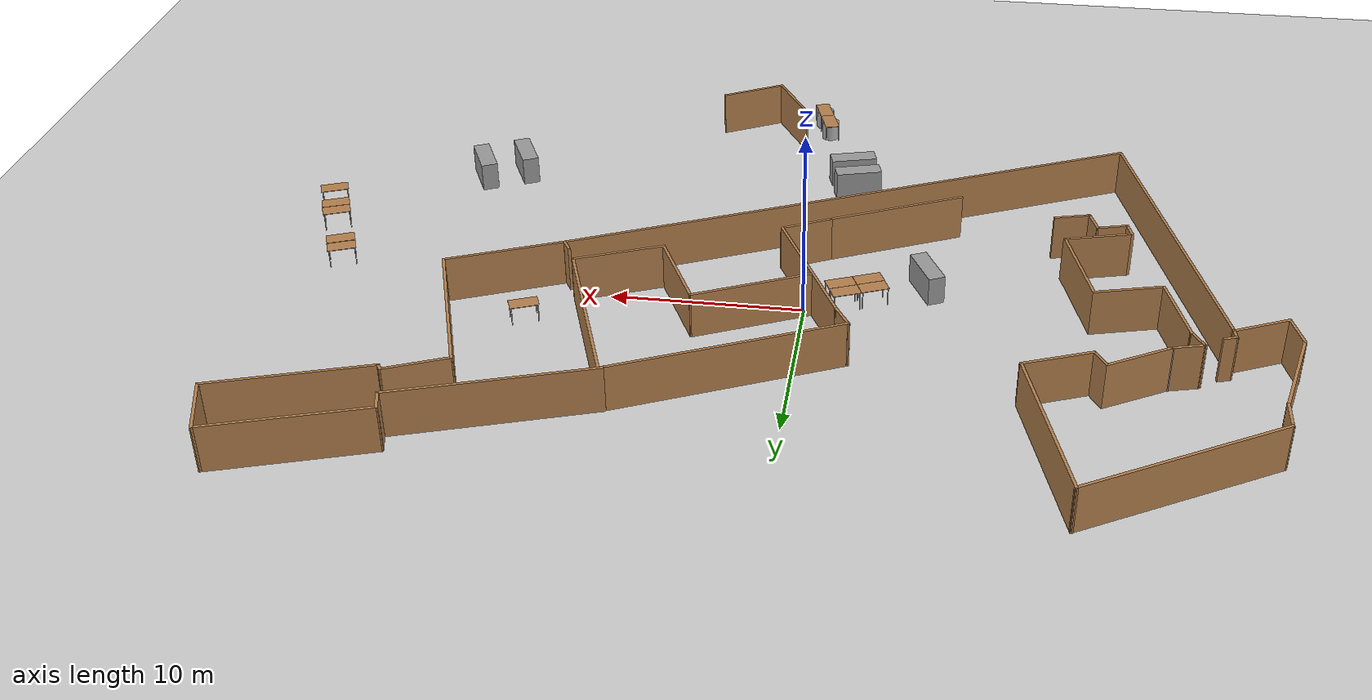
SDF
<sdf version="1.10">
 <world name="maze">
  <physics name="1ms" type="ignored">
   <max_step_size>0.0030000000000000001</max_step_size>
   <real_time_factor>1</real_time_factor>
   <real_time_update_rate>1000</real_time_update_rate>
  </physics>
  <plugin name="gz::sim::systems::Physics" filename="gz-sim-physics-system"/>
  <plugin name="gz::sim::systems::UserCommands" filename="gz-sim-user-commands-system"/>
  <plugin name="gz::sim::systems::SceneBroadcaster" filename="gz-sim-scene-broadcaster-system"/>
  <plugin name="gz::sim::systems::Contact" filename="gz-sim-contact-system"/>
  <gravity>0 0 -9.8000000000000007</gravity>
  <magnetic_field>6.0000000000000002e-06 2.3e-05 -4.1999999999999998e-05</magnetic_field>
  <atmosphere type="adiabatic"/>
  <scene>
   <ambient>0.400000006 0.400000006 0.400000006 1</ambient>
   <background>0.699999988 0.699999988 0.699999988 1</background>
   <shadows>false</shadows>
  </scene>
  <model name="ground_plane">
   <static>true</static>
   <link name="link">
    <collision name="collision">
     <geometry><plane><normal>0 0 1</normal><size>100 100</size></plane></geometry>
    </collision>
    <visual name="visual">
     <geometry><plane><normal>0 0 1</normal><size>100 100</size></plane></geometry>
     <material>
      <ambient>0.800000012 0.800000012 0.800000012 1</ambient>
      <diffuse>0.800000012 0.800000012 0.800000012 1</diffuse>
      <specular>0.800000012 0.800000012 0.800000012 1</specular>
     </material>
     <plugin name="__default__" filename="__default__"/>
    </visual>
    <inertial>
     <mass>1</mass>
     <inertia><ixx>1</ixx><ixy>0</ixy><ixz>0</ixz><iyy>1</iyy><iyz>0</iyz><izz>1</izz></inertia>
    </inertial>
   </link>
   <plugin name="__default__" filename="__default__"/>
  </model>
  <model name="FullOfficeMap">
   <pose>1.1203000000000001 -1.71753 0 0 0 0</pose>
   <link name="Wall_11">
    <collision name="Wall_11_Collision">
     <geometry><box><size>3.77678 0.14999999999999999 2.5</size></box></geometry>
     <pose>0 0 1.25 0 0 0</pose>
    </collision>
    <visual name="Wall_11_Visual">
     <pose>0 0 1.25 0 0 0</pose>
     <geometry><box><size>3.77678 0.14999999999999999 2.5</size></box></geometry>
     <material>
      <script><uri>file:///usr/share/gz/gz-sim8/media/gazebo.material</uri><name>Gazebo/Wood</name></script>
      <ambient>1 1 1 1</ambient>
     </material>
     <meta><layer>0</layer></meta>
    </visual>
    <pose>-13.7263 7.8209400000000002 0 0 0 -2.7603800000000001</pose>
    <inertial>
     <mass>1</mass>
     <inertia><ixx>1</ixx><ixy>0</ixy><ixz>0</ixz><iyy>1</iyy><iyz>0</iyz><izz>1</izz></inertia>
    </inertial>
   </link>
   <link name="Wall_12">
    <collision name="Wall_12_Collision">
     <geometry><box><size>1.25 0.14999999999999999 2.5</size></box></geometry>
     <pose>0 0 1.25 0 0 0</pose>
    </collision>
    <visual name="Wall_12_Visual">
     <pose>0 0 1.25 0 0 0</pose>
     <geometry><box><size>1.25 0.14999999999999999 2.5</size></box></geometry>
     <material>
      <script><uri>file:///usr/share/gz/gz-sim8/media/gazebo.material</uri><name>Gazebo/Wood</name></script>
      <ambient>1 1 1 1</ambient>
     </material>
     <meta><layer>0</layer></meta>
    </visual>
    <pose>-15.730999999999968 7.6225900000000015 0 0 0 2.0944000000000007</pose>
    <inertial>
     <mass>1</mass>
     <inertia><ixx>1</ixx><ixy>0</ixy><ixz>0</ixz><iyy>1</iyy><iyz>0</iyz><izz>1</izz></inertia>
    </inertial>
   </link>
   <link name="Wall_23">
    <collision name="Wall_23_Collision">
     <geometry><box><size>3.75 0.14999999999999999 2.5</size></box></geometry>
     <pose>0 0 1.25 0 0 0</pose>
    </collision>
    <visual name="Wall_23_Visual">
     <pose>0 0 1.25 0 0 0</pose>
     <geometry><box><size>3.75 0.14999999999999999 2.5</size></box></geometry>
     <material>
      <script><uri>file:///usr/share/gz/gz-sim8/media/gazebo.material</uri><name>Gazebo/Wood</name></script>
      <ambient>1 1 1 1</ambient>
     </material>
     <meta><layer>0</layer></meta>
    </visual>
    <pose>-17.564899999999966 7.1989100000000006 0 0 0 -2.6179899999999998</pose>
    <inertial>
     <mass>1</mass>
     <inertia><ixx>1</ixx><ixy>0</ixy><ixz>0</ixz><iyy>1</iyy><iyz>0</iyz><izz>1</izz></inertia>
    </inertial>
   </link>
   <link name="Wall_24">
    <collision name="Wall_24_Collision">
     <geometry><box><size>0.14999999999999999 0.14999999999999999 2.5</size></box></geometry>
     <pose>0 0 1.25 0 0 0</pose>
    </collision>
    <visual name="Wall_24_Visual">
     <pose>0 0 1.25 0 0 0</pose>
     <geometry><box><size>0.14999999999999999 0.14999999999999999 2.5</size></box></geometry>
     <material>
      <script><uri>file:///usr/share/gz/gz-sim8/media/gazebo.material</uri><name>Gazebo/Grey</name></script>
      <ambient>1 1 1 1</ambient>
     </material>
     <meta><layer>0</layer></meta>
    </visual>
    <pose>-19.123699999999964 6.2989100000000038 0 0 0 -5.5511151231257815e-17</pose>
    <inertial>
     <mass>1</mass>
     <inertia><ixx>1</ixx><ixy>0</ixy><ixz>0</ixz><iyy>1</iyy><iyz>0</iyz><izz>1</izz></inertia>
    </inertial>
   </link>
   <link name="Wall_26">
    <collision name="Wall_26_Collision">
     <geometry><box><size>1.75 0.14999999999999999 2.5</size></box></geometry>
     <pose>0 0 1.25 0 0 0</pose>
    </collision>
    <visual name="Wall_26_Visual">
     <pose>0 0 1.25 0 0 0</pose>
     <geometry><box><size>1.75 0.14999999999999999 2.5</size></box></geometry>
     <material>
      <script><uri>file:///usr/share/gz/gz-sim8/media/gazebo.material</uri><name>Gazebo/Wood</name></script>
      <ambient>1 1 1 1</ambient>
     </material>
     <meta><layer>0</layer></meta>
    </visual>
    <pose>-19.896499999999961 6.0918500000000035 0 0 0 -2.8797899999999998</pose>
    <inertial>
     <mass>1</mass>
     <inertia><ixx>1</ixx><ixy>0</ixy><ixz>0</ixz><iyy>1</iyy><iyz>0</iyz><izz>1</izz></inertia>
    </inertial>
   </link>
   <link name="Wall_27">
    <collision name="Wall_27_Collision">
     <geometry><box><size>1.25 0.14999999999999999 2.5</size></box></geometry>
     <pose>0 0 1.25 0 0 0</pose>
    </collision>
    <visual name="Wall_27_Visual">
     <pose>0 0 1.25 0 0 0</pose>
     <geometry><box><size>1.25 0.14999999999999999 2.5</size></box></geometry>
     <material>
      <script><uri>file:///usr/share/gz/gz-sim8/media/gazebo.material</uri><name>Gazebo/Wood</name></script>
      <ambient>1 1 1 1</ambient>
     </material>
     <meta><layer>0</layer></meta>
    </visual>
    <pose>-20.394199999999962 5.4084800000000035 0 0 0 -1.0472000000000004</pose>
    <inertial>
     <mass>1</mass>
     <inertia><ixx>1</ixx><ixy>0</ixy><ixz>0</ixz><iyy>1</iyy><iyz>0</iyz><izz>1</izz></inertia>
    </inertial>
   </link>
   <link name="Wall_28">
    <collision name="Wall_28_Collision">
     <geometry><box><size>4.25 0.14999999999999999 2.5</size></box></geometry>
     <pose>0 0 1.25 0 0 0</pose>
    </collision>
    <visual name="Wall_28_Visual">
     <pose>0 0 1.25 0 0 0</pose>
     <geometry><box><size>4.25 0.14999999999999999 2.5</size></box></geometry>
     <material>
      <script><uri>file:///usr/share/gz/gz-sim8/media/gazebo.material</uri><name>Gazebo/Wood</name></script>
      <ambient>1 1 1 1</ambient>
     </material>
     <meta><layer>0</layer></meta>
    </visual>
    <pose>-19.588599999999964 2.9520200000000063 0 0 0 -1.3089999999999995</pose>
    <inertial>
     <mass>1</mass>
     <inertia><ixx>1</ixx><ixy>0</ixy><ixz>0</ixz><iyy>1</iyy><iyz>0</iyz><izz>1</izz></inertia>
    </inertial>
   </link>
   <link name="Wall_29">
    <collision name="Wall_29_Collision">
     <geometry><box><size>3.75 0.14999999999999999 2.5</size></box></geometry>
     <pose>0 0 1.25 0 0 0</pose>
    </collision>
    <visual name="Wall_29_Visual">
     <pose>0 0 1.25 0 0 0</pose>
     <geometry><box><size>3.75 0.14999999999999999 2.5</size></box></geometry>
     <material>
      <script><uri>file:///usr/share/gz/gz-sim8/media/gazebo.material</uri><name>Gazebo/Wood</name></script>
      <ambient>1 1 1 1</ambient>
     </material>
     <meta><layer>0</layer></meta>
    </visual>
    <pose>-17.31939999999997 1.4377500000000065 0 0 0 0.26179899999999995</pose>
    <inertial>
     <mass>1</mass>
     <inertia><ixx>1</ixx><ixy>0</ixy><ixz>0</ixz><iyy>1</iyy><iyz>0</iyz><izz>1</izz></inertia>
    </inertial>
   </link>
   <link name="Wall_3">
    <collision name="Wall_3_Collision">
     <geometry><box><size>9.25 0.14999999999999999 2.5</size></box></geometry>
     <pose>0 0 1.25 0 0 0</pose>
    </collision>
    <visual name="Wall_3_Visual">
     <pose>0 0 1.25 0 0 0</pose>
     <geometry><box><size>9.25 0.14999999999999999 2.5</size></box></geometry>
     <material>
      <script><uri>file:///usr/share/gz/gz-sim8/media/gazebo.material</uri><name>Gazebo/Wood</name></script>
      <ambient>1 1 1 1</ambient>
     </material>
     <meta><layer>0</layer></meta>
    </visual>
    <pose>-13.220699999999972 12.890599999999997 0 0 0 1.8326</pose>
    <inertial>
     <mass>1</mass>
     <inertia><ixx>1</ixx><ixy>0</ixy><ixz>0</ixz><iyy>1</iyy><iyz>0</iyz><izz>1</izz></inertia>
    </inertial>
   </link>
   <link name="Wall_30">
    <collision name="Wall_30_Collision">
     <geometry><box><size>5.25 0.14999999999999999 2.5</size></box></geometry>
     <pose>0 0 1.25 0 0 0</pose>
    </collision>
    <visual name="Wall_30_Visual">
     <pose>0 0 1.25 0 0 0</pose>
     <geometry><box><size>5.25 0.14999999999999999 2.5</size></box></geometry>
     <material>
      <script><uri>file:///usr/share/gz/gz-sim8/media/gazebo.material</uri><name>Gazebo/Wood</name></script>
      <ambient>1 1 1 1</ambient>
     </material>
     <meta><layer>0</layer></meta>
    </visual>
    <pose>-14.92069999999997 -0.55949099999998886 0 0 0 -1.3089999999999995</pose>
    <inertial>
     <mass>1</mass>
     <inertia><ixx>1</ixx><ixy>0</ixy><ixz>0</ixz><iyy>1</iyy><iyz>0</iyz><izz>1</izz></inertia>
    </inertial>
   </link>
   <link name="Wall_31">
    <collision name="Wall_31_Collision">
     <geometry><box><size>3.75 0.14999999999999999 2.5</size></box></geometry>
     <pose>0 0 1.25 0 0 0</pose>
    </collision>
    <visual name="Wall_31_Visual">
     <pose>0 0 1.25 0 0 0</pose>
     <geometry><box><size>3.75 0.14999999999999999 2.5</size></box></geometry>
     <material>
      <script><uri>file:///usr/share/gz/gz-sim8/media/gazebo.material</uri><name>Gazebo/Wood</name></script>
      <ambient>1 1 1 1</ambient>
     </material>
     <meta><layer>0</layer></meta>
    </visual>
    <pose>-15.999399999999969 -3.4884799999999867 0 0 0 -2.8797899999999998</pose>
    <inertial>
     <mass>1</mass>
     <inertia><ixx>1</ixx><ixy>0</ixy><ixz>0</ixz><iyy>1</iyy><iyz>0</iyz><izz>1</izz></inertia>
    </inertial>
   </link>
   <link name="Wall_32">
    <collision name="Wall_32_Collision">
     <geometry><box><size>1 0.14999999999999999 2.5</size></box></geometry>
     <pose>0 0 1.25 0 0 0</pose>
    </collision>
    <visual name="Wall_32_Visual">
     <pose>0 0 1.25 0 0 0</pose>
     <geometry><box><size>1 0.14999999999999999 2.5</size></box></geometry>
     <material>
      <script><uri>file:///usr/share/gz/gz-sim8/media/gazebo.material</uri><name>Gazebo/Wood</name></script>
      <ambient>1 1 1 1</ambient>
     </material>
     <meta><layer>0</layer></meta>
    </visual>
    <pose>-17.628099999999964 -4.3648699999999874 0 0 0 -1.3089999999999995</pose>
    <inertial>
     <mass>1</mass>
     <inertia><ixx>1</ixx><ixy>0</ixy><ixz>0</ixz><iyy>1</iyy><iyz>0</iyz><izz>1</izz></inertia>
    </inertial>
   </link>
   <link name="Wall_33">
    <collision name="Wall_33_Collision">
     <geometry><box><size>1.75 0.14999999999999999 2.5</size></box></geometry>
     <pose>0 0 1.25 0 0 0</pose>
    </collision>
    <visual name="Wall_33_Visual">
     <pose>0 0 1.25 0 0 0</pose>
     <geometry><box><size>1.75 0.14999999999999999 2.5</size></box></geometry>
     <material>
      <script><uri>file:///usr/share/gz/gz-sim8/media/gazebo.material</uri><name>Gazebo/Wood</name></script>
      <ambient>1 1 1 1</ambient>
     </material>
     <meta><layer>0</layer></meta>
    </visual>
    <pose>-16.745299999999968 -4.5683299999999871 0 0 0 0.26179899999999995</pose>
    <inertial>
     <mass>1</mass>
     <inertia><ixx>1</ixx><ixy>0</ixy><ixz>0</ixz><iyy>1</iyy><iyz>0</iyz><izz>1</izz></inertia>
    </inertial>
   </link>
   <link name="Wall_34">
    <collision name="Wall_34_Collision">
     <geometry><box><size>1.51474 0.14999999999999999 2.5</size></box></geometry>
     <pose>0 0 1.25 0 0 0</pose>
    </collision>
    <visual name="Wall_34_Visual">
     <pose>0 0 1.25 0 0 0</pose>
     <geometry><box><size>1.51474 0.14999999999999999 2.5</size></box></geometry>
     <material>
      <script><uri>file:///usr/share/gz/gz-sim8/media/gazebo.material</uri><name>Gazebo/Wood</name></script>
      <ambient>1 1 1 1</ambient>
     </material>
     <meta><layer>0</layer></meta>
    </visual>
    <pose>-15.771299999999973 -5.0132799999999857 0 0 0 -1.271329999999999</pose>
    <inertial>
     <mass>1</mass>
     <inertia><ixx>1</ixx><ixy>0</ixy><ixz>0</ixz><iyy>1</iyy><iyz>0</iyz><izz>1</izz></inertia>
    </inertial>
   </link>
   <link name="Wall_38">
    <collision name="Wall_38_Collision">
     <geometry><box><size>2 0.14999999999999999 2.5</size></box></geometry>
     <pose>0 0 1.25 0 0 0</pose>
    </collision>
    <visual name="Wall_38_Visual">
     <pose>0 0 1.25 0 0 0</pose>
     <geometry><box><size>2 0.14999999999999999 2.5</size></box></geometry>
     <material>
      <script><uri>file:///usr/share/gz/gz-sim8/media/gazebo.material</uri><name>Gazebo/Wood</name></script>
      <ambient>1 1 1 1</ambient>
     </material>
     <meta><layer>0</layer></meta>
    </visual>
    <pose>-14.676499999999972 -5.3726699999999834 0 0 0 0.26179899999999995</pose>
    <inertial>
     <mass>1</mass>
     <inertia><ixx>1</ixx><ixy>0</ixy><ixz>0</ixz><iyy>1</iyy><iyz>0</iyz><izz>1</izz></inertia>
    </inertial>
   </link>
   <link name="Wall_44">
    <collision name="Wall_44_Collision">
     <geometry><box><size>7.5791500000000003 0.14999999999999999 2.5</size></box></geometry>
     <pose>0 0 1.25 0 0 0</pose>
    </collision>
    <visual name="Wall_44_Visual">
     <pose>0 0 1.25 0 0 0</pose>
     <geometry><box><size>7.5791500000000003 0.14999999999999999 2.5</size></box></geometry>
     <material>
      <script><uri>file:///usr/share/gz/gz-sim8/media/gazebo.material</uri><name>Gazebo/Wood</name></script>
      <ambient>1 1 1 1</ambient>
     </material>
     <meta><layer>0</layer></meta>
    </visual>
    <pose>-5.3889199999999793 -5.0718599999999849 0 0 0 0.44372099999999998</pose>
    <inertial>
     <mass>1</mass>
     <inertia><ixx>1</ixx><ixy>0</ixy><ixz>0</ixz><iyy>1</iyy><iyz>0</iyz><izz>1</izz></inertia>
    </inertial>
   </link>
   <link name="Wall_45">
    <collision name="Wall_45_Collision">
     <geometry><box><size>2.9271500000000001 0.14999999999999999 2.5</size></box></geometry>
     <pose>0 0 1.25 0 0 0</pose>
    </collision>
    <visual name="Wall_45_Visual">
     <pose>0 0 1.25 0 0 0</pose>
     <geometry><box><size>2.9271500000000001 0.14999999999999999 2.5</size></box></geometry>
     <material>
      <script><uri>file:///usr/share/gz/gz-sim8/media/gazebo.material</uri><name>Gazebo/Wood</name></script>
      <ambient>1 1 1 1</ambient>
     </material>
     <meta><layer>0</layer></meta>
    </visual>
    <pose>-0.79515799999998116 -2.850079999999986 0 0 0 0.46857399999999982</pose>
    <inertial>
     <mass>1</mass>
     <inertia><ixx>1</ixx><ixy>0</ixy><ixz>0</ixz><iyy>1</iyy><iyz>0</iyz><izz>1</izz></inertia>
    </inertial>
   </link>
   <link name="Wall_46">
    <collision name="Wall_46_Collision">
     <geometry><box><size>8.2358399999999996 0.14999999999999999 2.5</size></box></geometry>
     <pose>0 0 1.25 0 0 0</pose>
    </collision>
    <visual name="Wall_46_Visual">
     <pose>0 0 1.25 0 0 0</pose>
     <geometry><box><size>8.2358399999999996 0.14999999999999999 2.5</size></box></geometry>
     <material>
      <script><uri>file:///usr/share/gz/gz-sim8/media/gazebo.material</uri><name>Gazebo/Wood</name></script>
      <ambient>1 1 1 1</ambient>
     </material>
     <meta><layer>0</layer></meta>
    </visual>
    <pose>-1.3151899999999817 1.4172500000000117 0 0 0 2.0209099999999993</pose>
    <inertial>
     <mass>1</mass>
     <inertia><ixx>1</ixx><ixy>0</ixy><ixz>0</ixz><iyy>1</iyy><iyz>0</iyz><izz>1</izz></inertia>
    </inertial>
   </link>
   <link name="Wall_47">
    <collision name="Wall_47_Collision">
     <geometry><box><size>1.5 0.14999999999999999 2.5</size></box></geometry>
     <pose>0 0 1.25 0 0 0</pose>
    </collision>
    <visual name="Wall_47_Visual">
     <pose>0 0 1.25 0 0 0</pose>
     <geometry><box><size>1.5 0.14999999999999999 2.5</size></box></geometry>
     <material>
      <script><uri>file:///usr/share/gz/gz-sim8/media/gazebo.material</uri><name>Gazebo/Wood</name></script>
      <ambient>1 1 1 1</ambient>
     </material>
     <meta><layer>0</layer></meta>
    </visual>
    <pose>-3.4116299999999811 5.6420600000000052 0 0 0 2.0944000000000007</pose>
    <inertial>
     <mass>1</mass>
     <inertia><ixx>1</ixx><ixy>0</ixy><ixz>0</ixz><iyy>1</iyy><iyz>0</iyz><izz>1</izz></inertia>
    </inertial>
   </link>
   <link name="Wall_48">
    <collision name="Wall_48_Collision">
     <geometry><box><size>12.4849 0.14999999999999999 2.5</size></box></geometry>
     <pose>0 0 1.25 0 0 0</pose>
    </collision>
    <visual name="Wall_48_Visual">
     <pose>0 0 1.25 0 0 0</pose>
     <geometry><box><size>12.4849 0.14999999999999999 2.5</size></box></geometry>
     <material>
      <script><uri>file:///usr/share/gz/gz-sim8/media/gazebo.material</uri><name>Gazebo/Wood</name></script>
      <ambient>1 1 1 1</ambient>
     </material>
     <meta><layer>0</layer></meta>
    </visual>
    <pose>1.8449600000000146 8.8234799999999964 0 0 0 0.43461199999999967</pose>
    <inertial>
     <mass>1</mass>
     <inertia><ixx>1</ixx><ixy>0</ixy><ixz>0</ixz><iyy>1</iyy><iyz>0</iyz><izz>1</izz></inertia>
    </inertial>
   </link>
   <link name="Wall_49">
    <collision name="Wall_49_Collision">
     <geometry><box><size>9.9185499999999998 0.14999999999999999 2.5</size></box></geometry>
     <pose>0 0 1.25 0 0 0</pose>
    </collision>
    <visual name="Wall_49_Visual">
     <pose>0 0 1.25 0 0 0</pose>
     <geometry><box><size>9.9185499999999998 0.14999999999999999 2.5</size></box></geometry>
     <material>
      <script><uri>file:///usr/share/gz/gz-sim8/media/gazebo.material</uri><name>Gazebo/Wood</name></script>
      <ambient>1 1 1 1</ambient>
     </material>
     <meta><layer>0</layer></meta>
    </visual>
    <pose>9.0572700000000061 6.8119199999999998 0 0 0 -1.2330999999999994</pose>
    <inertial>
     <mass>1</mass>
     <inertia><ixx>1</ixx><ixy>0</ixy><ixz>0</ixz><iyy>1</iyy><iyz>0</iyz><izz>1</izz></inertia>
    </inertial>
   </link>
   <link name="Wall_5">
    <collision name="Wall_5_Collision">
     <geometry><box><size>11.25 0.14999999999999999 2.5</size></box></geometry>
     <pose>0 0 1.25 0 0 0</pose>
    </collision>
    <visual name="Wall_5_Visual">
     <pose>0 0 1.25 0 0 0</pose>
     <geometry><box><size>11.25 0.14999999999999999 2.5</size></box></geometry>
     <material>
      <script><uri>file:///usr/share/gz/gz-sim8/media/gazebo.material</uri><name>Gazebo/Wood</name></script>
      <ambient>1 1 1 1</ambient>
     </material>
     <meta><layer>0</layer></meta>
    </visual>
    <pose>-19.204799999999963 14.510499999999992 0 0 0 -2.6179899999999998</pose>
    <inertial>
     <mass>1</mass>
     <inertia><ixx>1</ixx><ixy>0</ixy><ixz>0</ixz><iyy>1</iyy><iyz>0</iyz><izz>1</izz></inertia>
    </inertial>
   </link>
   <link name="Wall_50">
    <collision name="Wall_50_Collision">
     <geometry><box><size>4.8802000000000003 0.14999999999999999 2.5</size></box></geometry>
     <pose>0 0 1.25 0 0 0</pose>
    </collision>
    <visual name="Wall_50_Visual">
     <pose>0 0 1.25 0 0 0</pose>
     <geometry><box><size>4.8802000000000003 0.14999999999999999 2.5</size></box></geometry>
     <material>
      <script><uri>file:///usr/share/gz/gz-sim8/media/gazebo.material</uri><name>Gazebo/Wood</name></script>
      <ambient>1 1 1 1</ambient>
     </material>
     <meta><layer>0</layer></meta>
    </visual>
    <pose>8.4944100000000056 1.2888600000000121 0 0 0 -2.74451</pose>
    <inertial>
     <mass>1</mass>
     <inertia><ixx>1</ixx><ixy>0</ixy><ixz>0</ixz><iyy>1</iyy><iyz>0</iyz><izz>1</izz></inertia>
    </inertial>
   </link>
   <link name="Wall_51">
    <collision name="Wall_51_Collision">
     <geometry><box><size>4.9959899999999999 0.14999999999999999 2.5</size></box></geometry>
     <pose>0 0 1.25 0 0 0</pose>
    </collision>
    <visual name="Wall_51_Visual">
     <pose>0 0 1.25 0 0 0</pose>
     <geometry><box><size>4.9959899999999999 0.14999999999999999 2.5</size></box></geometry>
     <material>
      <script><uri>file:///usr/share/gz/gz-sim8/media/gazebo.material</uri><name>Gazebo/Wood</name></script>
      <ambient>1 1 1 1</ambient>
     </material>
     <meta><layer>0</layer></meta>
    </visual>
    <pose>5.2579700000000109 2.5552900000000118 0 0 0 2.0214599999999998</pose>
    <inertial>
     <mass>1</mass>
     <inertia><ixx>1</ixx><ixy>0</ixy><ixz>0</ixz><iyy>1</iyy><iyz>0</iyz><izz>1</izz></inertia>
    </inertial>
   </link>
   <link name="Wall_52">
    <collision name="Wall_52_Collision">
     <geometry><box><size>6.4449399999999999 0.14999999999999999 2.5</size></box></geometry>
     <pose>0 0 1.25 0 0 0</pose>
    </collision>
    <visual name="Wall_52_Visual">
     <pose>0 0 1.25 0 0 0</pose>
     <geometry><box><size>6.4449399999999999 0.14999999999999999 2.5</size></box></geometry>
     <material>
      <script><uri>file:///usr/share/gz/gz-sim8/media/gazebo.material</uri><name>Gazebo/Wood</name></script>
      <ambient>1 1 1 1</ambient>
     </material>
     <meta><layer>0</layer></meta>
    </visual>
    <pose>1.3531200000000148 3.3995800000000056 0 0 0 -2.7029399999999999</pose>
    <inertial>
     <mass>1</mass>
     <inertia><ixx>1</ixx><ixy>0</ixy><ixz>0</ixz><iyy>1</iyy><iyz>0</iyz><izz>1</izz></inertia>
    </inertial>
   </link>
   <link name="Wall_54">
    <pose>-19.823799999999974 -4.2155299999999887 0 0 0 -1.3089999999999995</pose>
    <visual name="Wall_54_Visual">
     <pose>0 0 1.25 0 0 0</pose>
     <geometry><box><size>18 0.14999999999999999 2.5</size></box></geometry>
     <material>
      <script><uri>file:///usr/share/gz/gz-sim8/media/gazebo.material</uri><name>Gazebo/Wood</name></script>
      <ambient>1 1 1 1</ambient>
     </material>
    </visual>
    <collision name="Wall_54_Collision">
     <pose>0 0 1.25 0 0 0</pose>
     <geometry><box><size>18 0.14999999999999999 2.5</size></box></geometry>
    </collision>
    <inertial>
     <mass>1</mass>
     <inertia><ixx>1</ixx><ixy>0</ixy><ixz>0</ixz><iyy>1</iyy><iyz>0</iyz><izz>1</izz></inertia>
    </inertial>
   </link>
   <link name="Wall_57">
    <collision name="Wall_57_Collision">
     <geometry><box><size>32.113 0.14999999999999999 2.5</size></box></geometry>
     <pose>0 0 1.25 0 0 0</pose>
    </collision>
    <visual name="Wall_57_Visual">
     <pose>0 0 1.25 0 0 0</pose>
     <geometry><box><size>32.113 0.14999999999999999 2.5</size></box></geometry>
     <material>
      <script><uri>file:///usr/share/gz/gz-sim8/media/gazebo.material</uri><name>Gazebo/Wood</name></script>
      <ambient>1 1 1 1</ambient>
     </material>
     <meta><layer>0</layer></meta>
    </visual>
    <pose>-3.0222599999999797 -6.0983599999999836 0 0 0 0.43522699999999981</pose>
    <inertial>
     <mass>1</mass>
     <inertia><ixx>1</ixx><ixy>0</ixy><ixz>0</ixz><iyy>1</iyy><iyz>0</iyz><izz>1</izz></inertia>
    </inertial>
   </link>
   <link name="Wall_58">
    <collision name="Wall_58_Collision">
     <geometry><box><size>6.4132100000000003 0.14999999999999999 2.5</size></box></geometry>
     <pose>0 0 1.25 0 0 0</pose>
    </collision>
    <visual name="Wall_58_Visual">
     <pose>0 0 1.25 0 0 0</pose>
     <geometry><box><size>6.4132100000000003 0.14999999999999999 2.5</size></box></geometry>
     <material>
      <script><uri>file:///usr/share/gz/gz-sim8/media/gazebo.material</uri><name>Gazebo/Wood</name></script>
      <ambient>1 1 1 1</ambient>
     </material>
     <meta><layer>0</layer></meta>
    </visual>
    <pose>14.345800000000004 1.8777800000000102 0 0 0 0.40645099999999995</pose>
    <inertial>
     <mass>1</mass>
     <inertia><ixx>1</ixx><ixy>0</ixy><ixz>0</ixz><iyy>1</iyy><iyz>0</iyz><izz>1</izz></inertia>
    </inertial>
   </link>
   <link name="Wall_6">
    <collision name="Wall_6_Collision">
     <geometry><box><size>1.75 0.14999999999999999 2.5</size></box></geometry>
     <pose>0 0 1.25 0 0 0</pose>
    </collision>
    <visual name="Wall_6_Visual">
     <pose>0 0 1.25 0 0 0</pose>
     <geometry><box><size>1.75 0.14999999999999999 2.5</size></box></geometry>
     <material>
      <script><uri>file:///usr/share/gz/gz-sim8/media/gazebo.material</uri><name>Gazebo/Wood</name></script>
      <ambient>1 1 1 1</ambient>
     </material>
     <meta><layer>0</layer></meta>
    </visual>
    <pose>-24.01119999999996 10.935499999999998 0 0 0 -1.5708000000000004</pose>
    <inertial>
     <mass>1</mass>
     <inertia><ixx>1</ixx><ixy>0</ixy><ixz>0</ixz><iyy>1</iyy><iyz>0</iyz><izz>1</izz></inertia>
    </inertial>
   </link>
   <link name="Wall_60">
    <collision name="Wall_60_Collision">
     <geometry><box><size>8.9857899999999997 0.14999999999999999 2.5</size></box></geometry>
     <pose>0 0 1.25 0 0 0</pose>
    </collision>
    <visual name="Wall_60_Visual">
     <pose>0 0 1.25 0 0 0</pose>
     <geometry><box><size>8.9857899999999997 0.14999999999999999 2.5</size></box></geometry>
     <material>
      <script><uri>file:///usr/share/gz/gz-sim8/media/gazebo.material</uri><name>Gazebo/Wood</name></script>
      <ambient>1 1 1 1</ambient>
     </material>
     <meta><layer>0</layer></meta>
    </visual>
    <pose>15.829500000000003 7.3084499999999997 0 0 0 1.8915399999999991</pose>
    <inertial>
     <mass>1</mass>
     <inertia><ixx>1</ixx><ixy>0</ixy><ixz>0</ixz><iyy>1</iyy><iyz>0</iyz><izz>1</izz></inertia>
    </inertial>
   </link>
   <link name="Wall_61">
    <collision name="Wall_61_Collision">
     <geometry><box><size>3.4491999999999998 0.14999999999999999 2.5</size></box></geometry>
     <pose>0 0 1.25 0 0 0</pose>
    </collision>
    <visual name="Wall_61_Visual">
     <pose>0 0 1.25 0 0 0</pose>
     <geometry><box><size>3.4491999999999998 0.14999999999999999 2.5</size></box></geometry>
     <material>
      <script><uri>file:///usr/share/gz/gz-sim8/media/gazebo.material</uri><name>Gazebo/Wood</name></script>
      <ambient>1 1 1 1</ambient>
     </material>
     <meta><layer>0</layer></meta>
    </visual>
    <pose>15.951599999999999 12.153699999999994 0 0 0 0.40678100000000006</pose>
    <inertial>
     <mass>1</mass>
     <inertia><ixx>1</ixx><ixy>0</ixy><ixz>0</ixz><iyy>1</iyy><iyz>0</iyz><izz>1</izz></inertia>
    </inertial>
   </link>
   <link name="Wall_62">
    <collision name="Wall_62_Collision">
     <geometry><box><size>0.5 0.14999999999999999 2.5</size></box></geometry>
     <pose>0 0 1.25 0 0 0</pose>
    </collision>
    <visual name="Wall_62_Visual">
     <pose>0 0 1.25 0 0 0</pose>
     <geometry><box><size>0.5 0.14999999999999999 2.5</size></box></geometry>
     <material>
      <script><uri>file:///usr/share/gz/gz-sim8/media/gazebo.material</uri><name>Gazebo/Wood</name></script>
      <ambient>1 1 1 1</ambient>
     </material>
     <meta><layer>0</layer></meta>
    </visual>
    <pose>17.554099999999995 12.654799999999998 0 0 0 -1.0472000000000004</pose>
    <inertial>
     <mass>1</mass>
     <inertia><ixx>1</ixx><ixy>0</ixy><ixz>0</ixz><iyy>1</iyy><iyz>0</iyz><izz>1</izz></inertia>
    </inertial>
   </link>
   <link name="Wall_63">
    <collision name="Wall_63_Collision">
     <geometry><box><size>8.3035800000000002 0.14999999999999999 2.5</size></box></geometry>
     <pose>0 0 1.25 0 0 0</pose>
    </collision>
    <visual name="Wall_63_Visual">
     <pose>0 0 1.25 0 0 0</pose>
     <geometry><box><size>8.3035800000000002 0.14999999999999999 2.5</size></box></geometry>
     <material>
      <script><uri>file:///usr/share/gz/gz-sim8/media/gazebo.material</uri><name>Gazebo/Wood</name></script>
      <ambient>1 1 1 1</ambient>
     </material>
     <meta><layer>0</layer></meta>
    </visual>
    <pose>21.517399999999999 13.767499999999995 0 0 0 0.31530399999999997</pose>
    <inertial>
     <mass>1</mass>
     <inertia><ixx>1</ixx><ixy>0</ixy><ixz>0</ixz><iyy>1</iyy><iyz>0</iyz><izz>1</izz></inertia>
    </inertial>
   </link>
   <link name="Wall_64">
    <collision name="Wall_64_Collision">
     <geometry><box><size>3.4480599999999999 0.14999999999999999 2.5</size></box></geometry>
     <pose>0 0 1.25 0 0 0</pose>
    </collision>
    <visual name="Wall_64_Visual">
     <pose>0 0 1.25 0 0 0</pose>
     <geometry><box><size>3.4480599999999999 0.14999999999999999 2.5</size></box></geometry>
     <material>
      <script><uri>file:///usr/share/gz/gz-sim8/media/gazebo.material</uri><name>Gazebo/Wood</name></script>
      <ambient>1 1 1 1</ambient>
     </material>
     <meta><layer>0</layer></meta>
    </visual>
    <pose>24.885599999999993 16.600699999999986 0 0 0 1.8836999999999986</pose>
    <inertial>
     <mass>1</mass>
     <inertia><ixx>1</ixx><ixy>0</ixy><ixz>0</ixz><iyy>1</iyy><iyz>0</iyz><izz>1</izz></inertia>
    </inertial>
   </link>
   <link name="Wall_65">
    <collision name="Wall_65_Collision">
     <geometry><box><size>8.2053399999999996 0.14999999999999999 2.5</size></box></geometry>
     <pose>0 0 1.25 0 0 0</pose>
    </collision>
    <visual name="Wall_65_Visual">
     <pose>0 0 1.25 0 0 0</pose>
     <geometry><box><size>8.2053399999999996 0.14999999999999999 2.5</size></box></geometry>
     <material>
      <script><uri>file:///usr/share/gz/gz-sim8/media/gazebo.material</uri><name>Gazebo/Wood</name></script>
      <ambient>1 1 1 1</ambient>
     </material>
     <meta><layer>0</layer></meta>
    </visual>
    <pose>20.547899999999995 16.923699999999986 0 0 0 -2.8270900000000001</pose>
    <inertial>
     <mass>1</mass>
     <inertia><ixx>1</ixx><ixy>0</ixy><ixz>0</ixz><iyy>1</iyy><iyz>0</iyz><izz>1</izz></inertia>
    </inertial>
   </link>
   <link name="Wall_66">
    <collision name="Wall_66_Collision">
     <geometry><box><size>1.25 0.14999999999999999 2.5</size></box></geometry>
     <pose>0 0 1.25 0 0 0</pose>
    </collision>
    <visual name="Wall_66_Visual">
     <pose>0 0 1.25 0 0 0</pose>
     <geometry><box><size>1.25 0.14999999999999999 2.5</size></box></geometry>
     <material>
      <script><uri>file:///usr/share/gz/gz-sim8/media/gazebo.material</uri><name>Gazebo/Wood</name></script>
      <ambient>1 1 1 1</ambient>
     </material>
     <meta><layer>0</layer></meta>
    </visual>
    <pose>16.860099999999999 15.146499999999993 0 0 0 -1.3089999999999995</pose>
    <inertial>
     <mass>1</mass>
     <inertia><ixx>1</ixx><ixy>0</ixy><ixz>0</ixz><iyy>1</iyy><iyz>0</iyz><izz>1</izz></inertia>
    </inertial>
   </link>
   <link name="Wall_67">
    <collision name="Wall_67_Collision">
     <geometry><box><size>10.409800000000001 0.14999999999999999 2.5</size></box></geometry>
     <pose>0 0 1.25 0 0 0</pose>
    </collision>
    <visual name="Wall_67_Visual">
     <pose>0 0 1.25 0 0 0</pose>
     <geometry><box><size>10.409800000000001 0.14999999999999999 2.5</size></box></geometry>
     <material>
      <script><uri>file:///usr/share/gz/gz-sim8/media/gazebo.material</uri><name>Gazebo/Wood</name></script>
      <ambient>1 1 1 1</ambient>
     </material>
     <meta><layer>0</layer></meta>
    </visual>
    <pose>12.134700000000006 12.996299999999994 0 0 0 -2.8205</pose>
    <inertial>
     <mass>1</mass>
     <inertia><ixx>1</ixx><ixy>0</ixy><ixz>0</ixz><iyy>1</iyy><iyz>0</iyz><izz>1</izz></inertia>
    </inertial>
   </link>
   <link name="Wall_7">
    <collision name="Wall_7_Collision">
     <geometry><box><size>5.5 0.14999999999999999 2.5</size></box></geometry>
     <pose>0 0 1.25 0 0 0</pose>
    </collision>
    <visual name="Wall_7_Visual">
     <pose>0 0 1.25 0 0 0</pose>
     <geometry><box><size>5.5 0.14999999999999999 2.5</size></box></geometry>
     <material>
      <script><uri>file:///usr/share/gz/gz-sim8/media/gazebo.material</uri><name>Gazebo/Wood</name></script>
      <ambient>1 1 1 1</ambient>
     </material>
     <meta><layer>0</layer></meta>
    </visual>
    <pose>-24.703599999999959 7.5516800000000002 0 0 0 -1.8326</pose>
    <inertial>
     <mass>1</mass>
     <inertia><ixx>1</ixx><ixy>0</ixy><ixz>0</ixz><iyy>1</iyy><iyz>0</iyz><izz>1</izz></inertia>
    </inertial>
   </link>
   <link name="Wall_74">
    <collision name="Wall_74_Collision">
     <geometry><box><size>0.76837999999999995 0.14999999999999999 2.5</size></box></geometry>
     <pose>0 0 1.25 0 0 0</pose>
    </collision>
    <visual name="Wall_74_Visual">
     <pose>0 0 1.25 0 0 0</pose>
     <geometry><box><size>0.76837999999999995 0.14999999999999999 2.5</size></box></geometry>
     <material>
      <script><uri>file:///usr/share/gz/gz-sim8/media/gazebo.material</uri><name>Gazebo/Wood</name></script>
      <ambient>1 1 1 1</ambient>
     </material>
     <meta><layer>0</layer></meta>
    </visual>
    <pose>-22.17559999999996 4.7117100000000045 0 0 0 1.7062899999999996</pose>
    <inertial>
     <mass>1</mass>
     <inertia><ixx>1</ixx><ixy>0</ixy><ixz>0</ixz><iyy>1</iyy><iyz>0</iyz><izz>1</izz></inertia>
    </inertial>
   </link>
   <link name="Wall_75">
    <collision name="Wall_75_Collision">
     <geometry><box><size>0.76818500000000001 0.14999999999999999 2.5</size></box></geometry>
     <pose>0 0 1.25 0 0 0</pose>
    </collision>
    <visual name="Wall_75_Visual">
     <pose>0 0 1.25 0 0 0</pose>
     <geometry><box><size>0.76818500000000001 0.14999999999999999 2.5</size></box></geometry>
     <material>
      <script><uri>file:///usr/share/gz/gz-sim8/media/gazebo.material</uri><name>Gazebo/Wood</name></script>
      <ambient>1 1 1 1</ambient>
     </material>
     <meta><layer>0</layer></meta>
    </visual>
    <pose>-21.92409999999996 5.1158100000000042 0 0 0 0.32175099999999979</pose>
    <inertial>
     <mass>1</mass>
     <inertia><ixx>1</ixx><ixy>0</ixy><ixz>0</ixz><iyy>1</iyy><iyz>0</iyz><izz>1</izz></inertia>
    </inertial>
   </link>
   <link name="Wall_78">
    <collision name="Wall_78_Collision">
     <geometry><box><size>0.86296799999999996 0.14999999999999999 2.5</size></box></geometry>
     <pose>0 0 1.25 0 0 0</pose>
    </collision>
    <visual name="Wall_78_Visual">
     <pose>0 0 1.25 0 0 0</pose>
     <geometry><box><size>0.86296799999999996 0.14999999999999999 2.5</size></box></geometry>
     <material>
      <script><uri>file:///usr/share/gz/gz-sim8/media/gazebo.material</uri><name>Gazebo/Wood</name></script>
      <ambient>1 1 1 1</ambient>
     </material>
     <meta><layer>0</layer></meta>
    </visual>
    <pose>11.29000000000001 0.947778000000012 0 0 0 2.0979899999999998</pose>
    <inertial>
     <mass>1</mass>
     <inertia><ixx>1</ixx><ixy>0</ixy><ixz>0</ixz><iyy>1</iyy><iyz>0</iyz><izz>1</izz></inertia>
    </inertial>
   </link>
   <link name="Wall_8">
    <collision name="Wall_8_Collision">
     <geometry><box><size>2 0.14999999999999999 2.5</size></box></geometry>
     <pose>0 0 1.25 0 0 0</pose>
    </collision>
    <visual name="Wall_8_Visual">
     <pose>0 0 1.25 0 0 0</pose>
     <geometry><box><size>2 0.14999999999999999 2.5</size></box></geometry>
     <material>
      <script><uri>file:///usr/share/gz/gz-sim8/media/gazebo.material</uri><name>Gazebo/Wood</name></script>
      <ambient>1 1 1 1</ambient>
     </material>
     <meta><layer>0</layer></meta>
    </visual>
    <pose>-25.156499999999959 4.0743500000000008 0 0 0 -1.3089999999999995</pose>
    <inertial>
     <mass>1</mass>
     <inertia><ixx>1</ixx><ixy>0</ixy><ixz>0</ixz><iyy>1</iyy><iyz>0</iyz><izz>1</izz></inertia>
    </inertial>
   </link>
   <link name="Wall_9">
    <collision name="Wall_9_Collision">
     <geometry><box><size>3.2197499999999999 0.14999999999999999 2.5</size></box></geometry>
     <pose>0 0 1.25 0 0 0</pose>
    </collision>
    <visual name="Wall_9_Visual">
     <pose>0 0 1.25 0 0 0</pose>
     <geometry><box><size>3.2197499999999999 0.14999999999999999 2.5</size></box></geometry>
     <material>
      <script><uri>file:///usr/share/gz/gz-sim8/media/gazebo.material</uri><name>Gazebo/Wood</name></script>
      <ambient>1 1 1 1</ambient>
     </material>
     <meta><layer>0</layer></meta>
    </visual>
    <pose>-23.525399999999962 3.8282900000000044 0 0 0 0.43543699999999952</pose>
    <inertial>
     <mass>1</mass>
     <inertia><ixx>1</ixx><ixy>0</ixy><ixz>0</ixz><iyy>1</iyy><iyz>0</iyz><izz>1</izz></inertia>
    </inertial>
   </link>
   <static>true</static>
  </model>
  <model name="Wall_40_new">
   <static>true</static>
   <pose>2.6091833114624023 -18.863498687744141 0 0 0 -1.0472000210755694</pose>
   <link name="link">
    <collision name="collision">
     <geometry><box><size>3.75 0.14999999999999999 2.5</size></box></geometry>
     <pose>0 0 1.25 0 0 0</pose>
    </collision>
    <visual name="visual">
     <pose>0 0 1.25 0 0 0</pose>
     <geometry><box><size>3.75 0.14999999999999999 2.5</size></box></geometry>
     <material>
      <script><uri>file:///usr/share/gz/gz-sim8/media/gazebo.material</uri><name>Gazebo/Wood</name></script>
      <ambient>1 1 1 1</ambient>
     </material>
    </visual>
    <inertial>
     <mass>1</mass>
     <inertia><ixx>1</ixx><ixy>0</ixy><ixz>0</ixz><iyy>1</iyy><iyz>0</iyz><izz>1</izz></inertia>
    </inertial>
   </link>
  </model>
  <model name="table_0_clone_1">
   <static>true</static>
   <link name="link">
    <collision name="surface">
     <pose>0 0 1 0 0 0</pose>
     <geometry><box><size>1.5 0.80000000000000004 0.029999999999999999</size></box></geometry>
     <surface><friction><ode><mu>0.59999999999999998</mu><mu2>0.59999999999999998</mu2></ode></friction></surface>
    </collision>
    <visual name="visual1">
     <pose>0 0 1 0 0 0</pose>
     <geometry><box><size>1.5 0.80000000000000004 0.029999999999999999</size></box></geometry>
     <material>
      <script><uri>file:///usr/share/gz/gz-sim8/media/gazebo.material</uri><name>Gazebo/Wood</name></script>
     </material>
    </visual>
    <collision name="front_left_leg">
     <pose>0.68000000000000005 0.38 0.5 0 0 0</pose>
     <geometry><cylinder><radius>0.02</radius><length>1</length></cylinder></geometry>
    </collision>
    <visual name="front_left_leg">
     <pose>0.68000000000000005 0.38 0.5 0 0 0</pose>
     <geometry><cylinder><radius>0.02</radius><length>1</length></cylinder></geometry>
     <material>
      <script><uri>file:///usr/share/gz/gz-sim8/media/gazebo.material</uri><name>Gazebo/Grey</name></script>
     </material>
    </visual>
    <collision name="front_right_leg">
     <pose>0.68000000000000005 -0.38 0.5 0 0 0</pose>
     <geometry><cylinder><radius>0.02</radius><length>1</length></cylinder></geometry>
    </collision>
    <visual name="front_right_leg">
     <pose>0.68000000000000005 -0.38 0.5 0 0 0</pose>
     <geometry><cylinder><radius>0.02</radius><length>1</length></cylinder></geometry>
     <material>
      <script><uri>file:///usr/share/gz/gz-sim8/media/gazebo.material</uri><name>Gazebo/Grey</name></script>
     </material>
    </visual>
    <collision name="back_right_leg">
     <pose>-0.68000000000000005 -0.38 0.5 0 0 0</pose>
     <geometry><cylinder><radius>0.02</radius><length>1</length></cylinder></geometry>
    </collision>
    <visual name="back_right_leg">
     <pose>-0.68000000000000005 -0.38 0.5 0 0 0</pose>
     <geometry><cylinder><radius>0.02</radius><length>1</length></cylinder></geometry>
     <material>
      <script><uri>file:///usr/share/gz/gz-sim8/media/gazebo.material</uri><name>Gazebo/Grey</name></script>
     </material>
    </visual>
    <collision name="back_left_leg">
     <pose>-0.68000000000000005 0.38 0.5 0 0 0</pose>
     <geometry><cylinder><radius>0.02</radius><length>1</length></cylinder></geometry>
    </collision>
    <visual name="back_left_leg">
     <pose>-0.68000000000000005 0.38 0.5 0 0 0</pose>
     <geometry><cylinder><radius>0.02</radius><length>1</length></cylinder></geometry>
     <material>
      <script><uri>file:///usr/share/gz/gz-sim8/media/gazebo.material</uri><name>Gazebo/Grey</name></script>
     </material>
    </visual>
    <inertial>
     <mass>1</mass>
     <inertia><ixx>1</ixx><ixy>0</ixy><ixz>0</ixz><iyy>1</iyy><iyz>0</iyz><izz>1</izz></inertia>
    </inertial>
   </link>
   <pose>13.972799999999999 2.6148899999999999 0 0 0 0.39148299999999986</pose>
  </model>
  <model name="table_0_clone_1_1">
   <static>true</static>
   <link name="link">
    <collision name="surface">
     <pose>0 0 1 0 0 0</pose>
     <geometry><box><size>1.5 0.80000000000000004 0.029999999999999999</size></box></geometry>
     <surface><friction><ode><mu>0.59999999999999998</mu><mu2>0.59999999999999998</mu2></ode></friction></surface>
    </collision>
    <visual name="visual1">
     <pose>0 0 1 0 0 0</pose>
     <geometry><box><size>1.5 0.80000000000000004 0.029999999999999999</size></box></geometry>
     <material>
      <script><uri>file:///usr/share/gz/gz-sim8/media/gazebo.material</uri><name>Gazebo/Wood</name></script>
     </material>
    </visual>
    <collision name="front_left_leg">
     <pose>0.68000000000000005 0.38 0.5 0 0 0</pose>
     <geometry><cylinder><radius>0.02</radius><length>1</length></cylinder></geometry>
    </collision>
    <visual name="front_left_leg">
     <pose>0.68000000000000005 0.38 0.5 0 0 0</pose>
     <geometry><cylinder><radius>0.02</radius><length>1</length></cylinder></geometry>
     <material>
      <script><uri>file:///usr/share/gz/gz-sim8/media/gazebo.material</uri><name>Gazebo/Grey</name></script>
     </material>
    </visual>
    <collision name="front_right_leg">
     <pose>0.68000000000000005 -0.38 0.5 0 0 0</pose>
     <geometry><cylinder><radius>0.02</radius><length>1</length></cylinder></geometry>
    </collision>
    <visual name="front_right_leg">
     <pose>0.68000000000000005 -0.38 0.5 0 0 0</pose>
     <geometry><cylinder><radius>0.02</radius><length>1</length></cylinder></geometry>
     <material>
      <script><uri>file:///usr/share/gz/gz-sim8/media/gazebo.material</uri><name>Gazebo/Grey</name></script>
     </material>
    </visual>
    <collision name="back_right_leg">
     <pose>-0.68000000000000005 -0.38 0.5 0 0 0</pose>
     <geometry><cylinder><radius>0.02</radius><length>1</length></cylinder></geometry>
    </collision>
    <visual name="back_right_leg">
     <pose>-0.68000000000000005 -0.38 0.5 0 0 0</pose>
     <geometry><cylinder><radius>0.02</radius><length>1</length></cylinder></geometry>
     <material>
      <script><uri>file:///usr/share/gz/gz-sim8/media/gazebo.material</uri><name>Gazebo/Grey</name></script>
     </material>
    </visual>
    <collision name="back_left_leg">
     <pose>-0.68000000000000005 0.38 0.5 0 0 0</pose>
     <geometry><cylinder><radius>0.02</radius><length>1</length></cylinder></geometry>
    </collision>
    <visual name="back_left_leg">
     <pose>-0.68000000000000005 0.38 0.5 0 0 0</pose>
     <geometry><cylinder><radius>0.02</radius><length>1</length></cylinder></geometry>
     <material>
      <script><uri>file:///usr/share/gz/gz-sim8/media/gazebo.material</uri><name>Gazebo/Grey</name></script>
     </material>
    </visual>
    <inertial>
     <mass>1</mass>
     <inertia><ixx>1</ixx><ixy>0</ixy><ixz>0</ixz><iyy>1</iyy><iyz>0</iyz><izz>1</izz></inertia>
    </inertial>
   </link>
   <pose>26.739439386883607 -5.8970177628243707 0 0 0 0.39148302161510867</pose>
  </model>
  <model name="table_0_clone_1_2">
   <static>true</static>
   <link name="link">
    <collision name="surface">
     <pose>0 0 1 0 0 0</pose>
     <geometry><box><size>1.5 0.80000000000000004 0.029999999999999999</size></box></geometry>
     <surface><friction><ode><mu>0.59999999999999998</mu><mu2>0.59999999999999998</mu2></ode></friction></surface>
    </collision>
    <visual name="visual1">
     <pose>0 0 1 0 0 0</pose>
     <geometry><box><size>1.5 0.80000000000000004 0.029999999999999999</size></box></geometry>
     <material>
      <script><uri>file:///usr/share/gz/gz-sim8/media/gazebo.material</uri><name>Gazebo/Wood</name></script>
     </material>
    </visual>
    <collision name="front_left_leg">
     <pose>0.68000000000000005 0.38 0.5 0 0 0</pose>
     <geometry><cylinder><radius>0.02</radius><length>1</length></cylinder></geometry>
    </collision>
    <visual name="front_left_leg">
     <pose>0.68000000000000005 0.38 0.5 0 0 0</pose>
     <geometry><cylinder><radius>0.02</radius><length>1</length></cylinder></geometry>
     <material>
      <script><uri>file:///usr/share/gz/gz-sim8/media/gazebo.material</uri><name>Gazebo/Grey</name></script>
     </material>
    </visual>
    <collision name="front_right_leg">
     <pose>0.68000000000000005 -0.38 0.5 0 0 0</pose>
     <geometry><cylinder><radius>0.02</radius><length>1</length></cylinder></geometry>
    </collision>
    <visual name="front_right_leg">
     <pose>0.68000000000000005 -0.38 0.5 0 0 0</pose>
     <geometry><cylinder><radius>0.02</radius><length>1</length></cylinder></geometry>
     <material>
      <script><uri>file:///usr/share/gz/gz-sim8/media/gazebo.material</uri><name>Gazebo/Grey</name></script>
     </material>
    </visual>
    <collision name="back_right_leg">
     <pose>-0.68000000000000005 -0.38 0.5 0 0 0</pose>
     <geometry><cylinder><radius>0.02</radius><length>1</length></cylinder></geometry>
    </collision>
    <visual name="back_right_leg">
     <pose>-0.68000000000000005 -0.38 0.5 0 0 0</pose>
     <geometry><cylinder><radius>0.02</radius><length>1</length></cylinder></geometry>
     <material>
      <script><uri>file:///usr/share/gz/gz-sim8/media/gazebo.material</uri><name>Gazebo/Grey</name></script>
     </material>
    </visual>
    <collision name="back_left_leg">
     <pose>-0.68000000000000005 0.38 0.5 0 0 0</pose>
     <geometry><cylinder><radius>0.02</radius><length>1</length></cylinder></geometry>
    </collision>
    <visual name="back_left_leg">
     <pose>-0.68000000000000005 0.38 0.5 0 0 0</pose>
     <geometry><cylinder><radius>0.02</radius><length>1</length></cylinder></geometry>
     <material>
      <script><uri>file:///usr/share/gz/gz-sim8/media/gazebo.material</uri><name>Gazebo/Grey</name></script>
     </material>
    </visual>
    <inertial>
     <mass>1</mass>
     <inertia><ixx>1</ixx><ixy>0</ixy><ixz>0</ixz><iyy>1</iyy><iyz>0</iyz><izz>1</izz></inertia>
    </inertial>
   </link>
   <pose>26.443804289956802 -5.1302925006380224 0 0 0 0.39148302161510867</pose>
  </model>
  <model name="table_0_clone_1_3">
   <static>true</static>
   <link name="link">
    <collision name="surface">
     <pose>0 0 1 0 0 0</pose>
     <geometry><box><size>1.5 0.80000000000000004 0.029999999999999999</size></box></geometry>
     <surface><friction><ode><mu>0.59999999999999998</mu><mu2>0.59999999999999998</mu2></ode></friction></surface>
    </collision>
    <visual name="visual1">
     <pose>0 0 1 0 0 0</pose>
     <geometry><box><size>1.5 0.80000000000000004 0.029999999999999999</size></box></geometry>
     <material>
      <script><uri>file:///usr/share/gz/gz-sim8/media/gazebo.material</uri><name>Gazebo/Wood</name></script>
     </material>
    </visual>
    <collision name="front_left_leg">
     <pose>0.68000000000000005 0.38 0.5 0 0 0</pose>
     <geometry><cylinder><radius>0.02</radius><length>1</length></cylinder></geometry>
    </collision>
    <visual name="front_left_leg">
     <pose>0.68000000000000005 0.38 0.5 0 0 0</pose>
     <geometry><cylinder><radius>0.02</radius><length>1</length></cylinder></geometry>
     <material>
      <script><uri>file:///usr/share/gz/gz-sim8/media/gazebo.material</uri><name>Gazebo/Grey</name></script>
     </material>
    </visual>
    <collision name="front_right_leg">
     <pose>0.68000000000000005 -0.38 0.5 0 0 0</pose>
     <geometry><cylinder><radius>0.02</radius><length>1</length></cylinder></geometry>
    </collision>
    <visual name="front_right_leg">
     <pose>0.68000000000000005 -0.38 0.5 0 0 0</pose>
     <geometry><cylinder><radius>0.02</radius><length>1</length></cylinder></geometry>
     <material>
      <script><uri>file:///usr/share/gz/gz-sim8/media/gazebo.material</uri><name>Gazebo/Grey</name></script>
     </material>
    </visual>
    <collision name="back_right_leg">
     <pose>-0.68000000000000005 -0.38 0.5 0 0 0</pose>
     <geometry><cylinder><radius>0.02</radius><length>1</length></cylinder></geometry>
    </collision>
    <visual name="back_right_leg">
     <pose>-0.68000000000000005 -0.38 0.5 0 0 0</pose>
     <geometry><cylinder><radius>0.02</radius><length>1</length></cylinder></geometry>
     <material>
      <script><uri>file:///usr/share/gz/gz-sim8/media/gazebo.material</uri><name>Gazebo/Grey</name></script>
     </material>
    </visual>
    <collision name="back_left_leg">
     <pose>-0.68000000000000005 0.38 0.5 0 0 0</pose>
     <geometry><cylinder><radius>0.02</radius><length>1</length></cylinder></geometry>
    </collision>
    <visual name="back_left_leg">
     <pose>-0.68000000000000005 0.38 0.5 0 0 0</pose>
     <geometry><cylinder><radius>0.02</radius><length>1</length></cylinder></geometry>
     <material>
      <script><uri>file:///usr/share/gz/gz-sim8/media/gazebo.material</uri><name>Gazebo/Grey</name></script>
     </material>
    </visual>
    <inertial>
     <mass>1</mass>
     <inertia><ixx>1</ixx><ixy>0</ixy><ixz>0</ixz><iyy>1</iyy><iyz>0</iyz><izz>1</izz></inertia>
    </inertial>
   </link>
   <pose>27.361544148586177 -7.5154429326638379 0 0 0 0.39148302161510867</pose>
  </model>
  <model name="table_0_clone_1_4">
   <static>true</static>
   <link name="link">
    <collision name="surface">
     <pose>0 0 1 0 0 0</pose>
     <geometry><box><size>1.5 0.80000000000000004 0.029999999999999999</size></box></geometry>
     <surface><friction><ode><mu>0.59999999999999998</mu><mu2>0.59999999999999998</mu2></ode></friction></surface>
    </collision>
    <visual name="visual1">
     <pose>0 0 1 0 0 0</pose>
     <geometry><box><size>1.5 0.80000000000000004 0.029999999999999999</size></box></geometry>
     <material>
      <script><uri>file:///usr/share/gz/gz-sim8/media/gazebo.material</uri><name>Gazebo/Wood</name></script>
     </material>
    </visual>
    <collision name="front_left_leg">
     <pose>0.68000000000000005 0.38 0.5 0 0 0</pose>
     <geometry><cylinder><radius>0.02</radius><length>1</length></cylinder></geometry>
    </collision>
    <visual name="front_left_leg">
     <pose>0.68000000000000005 0.38 0.5 0 0 0</pose>
     <geometry><cylinder><radius>0.02</radius><length>1</length></cylinder></geometry>
     <material>
      <script><uri>file:///usr/share/gz/gz-sim8/media/gazebo.material</uri><name>Gazebo/Grey</name></script>
     </material>
    </visual>
    <collision name="front_right_leg">
     <pose>0.68000000000000005 -0.38 0.5 0 0 0</pose>
     <geometry><cylinder><radius>0.02</radius><length>1</length></cylinder></geometry>
    </collision>
    <visual name="front_right_leg">
     <pose>0.68000000000000005 -0.38 0.5 0 0 0</pose>
     <geometry><cylinder><radius>0.02</radius><length>1</length></cylinder></geometry>
     <material>
      <script><uri>file:///usr/share/gz/gz-sim8/media/gazebo.material</uri><name>Gazebo/Grey</name></script>
     </material>
    </visual>
    <collision name="back_right_leg">
     <pose>-0.68000000000000005 -0.38 0.5 0 0 0</pose>
     <geometry><cylinder><radius>0.02</radius><length>1</length></cylinder></geometry>
    </collision>
    <visual name="back_right_leg">
     <pose>-0.68000000000000005 -0.38 0.5 0 0 0</pose>
     <geometry><cylinder><radius>0.02</radius><length>1</length></cylinder></geometry>
     <material>
      <script><uri>file:///usr/share/gz/gz-sim8/media/gazebo.material</uri><name>Gazebo/Grey</name></script>
     </material>
    </visual>
    <collision name="back_left_leg">
     <pose>-0.68000000000000005 0.38 0.5 0 0 0</pose>
     <geometry><cylinder><radius>0.02</radius><length>1</length></cylinder></geometry>
    </collision>
    <visual name="back_left_leg">
     <pose>-0.68000000000000005 0.38 0.5 0 0 0</pose>
     <geometry><cylinder><radius>0.02</radius><length>1</length></cylinder></geometry>
     <material>
      <script><uri>file:///usr/share/gz/gz-sim8/media/gazebo.material</uri><name>Gazebo/Grey</name></script>
     </material>
    </visual>
    <inertial>
     <mass>1</mass>
     <inertia><ixx>1</ixx><ixy>0</ixy><ixz>0</ixz><iyy>1</iyy><iyz>0</iyz><izz>1</izz></inertia>
    </inertial>
   </link>
   <pose>25.233738594584153 -2.2790649815965267 0 0 0 0.39148302161510867</pose>
  </model>
  <model name="table_0_clone_1_4_1">
   <static>true</static>
   <link name="link">
    <collision name="surface">
     <pose>0 0 1 0 0 0</pose>
     <geometry><box><size>1.5 0.80000000000000004 0.029999999999999999</size></box></geometry>
     <surface><friction><ode><mu>0.59999999999999998</mu><mu2>0.59999999999999998</mu2></ode></friction></surface>
    </collision>
    <visual name="visual1">
     <pose>0 0 1 0 0 0</pose>
     <geometry><box><size>1.5 0.80000000000000004 0.029999999999999999</size></box></geometry>
     <material>
      <script><uri>file:///usr/share/gz/gz-sim8/media/gazebo.material</uri><name>Gazebo/Wood</name></script>
     </material>
    </visual>
    <collision name="front_left_leg">
     <pose>0.68000000000000005 0.38 0.5 0 0 0</pose>
     <geometry><cylinder><radius>0.02</radius><length>1</length></cylinder></geometry>
    </collision>
    <visual name="front_left_leg">
     <pose>0.68000000000000005 0.38 0.5 0 0 0</pose>
     <geometry><cylinder><radius>0.02</radius><length>1</length></cylinder></geometry>
     <material>
      <script><uri>file:///usr/share/gz/gz-sim8/media/gazebo.material</uri><name>Gazebo/Grey</name></script>
     </material>
    </visual>
    <collision name="front_right_leg">
     <pose>0.68000000000000005 -0.38 0.5 0 0 0</pose>
     <geometry><cylinder><radius>0.02</radius><length>1</length></cylinder></geometry>
    </collision>
    <visual name="front_right_leg">
     <pose>0.68000000000000005 -0.38 0.5 0 0 0</pose>
     <geometry><cylinder><radius>0.02</radius><length>1</length></cylinder></geometry>
     <material>
      <script><uri>file:///usr/share/gz/gz-sim8/media/gazebo.material</uri><name>Gazebo/Grey</name></script>
     </material>
    </visual>
    <collision name="back_right_leg">
     <pose>-0.68000000000000005 -0.38 0.5 0 0 0</pose>
     <geometry><cylinder><radius>0.02</radius><length>1</length></cylinder></geometry>
    </collision>
    <visual name="back_right_leg">
     <pose>-0.68000000000000005 -0.38 0.5 0 0 0</pose>
     <geometry><cylinder><radius>0.02</radius><length>1</length></cylinder></geometry>
     <material>
      <script><uri>file:///usr/share/gz/gz-sim8/media/gazebo.material</uri><name>Gazebo/Grey</name></script>
     </material>
    </visual>
    <collision name="back_left_leg">
     <pose>-0.68000000000000005 0.38 0.5 0 0 0</pose>
     <geometry><cylinder><radius>0.02</radius><length>1</length></cylinder></geometry>
    </collision>
    <visual name="back_left_leg">
     <pose>-0.68000000000000005 0.38 0.5 0 0 0</pose>
     <geometry><cylinder><radius>0.02</radius><length>1</length></cylinder></geometry>
     <material>
      <script><uri>file:///usr/share/gz/gz-sim8/media/gazebo.material</uri><name>Gazebo/Grey</name></script>
     </material>
    </visual>
    <inertial>
     <mass>1</mass>
     <inertia><ixx>1</ixx><ixy>0</ixy><ixz>0</ixz><iyy>1</iyy><iyz>0</iyz><izz>1</izz></inertia>
    </inertial>
   </link>
   <pose>24.925049812371064 -1.4957804955523417 0 0 0 0.39148302161510867</pose>
  </model>
  <model name="unit_box_clone_clone_1">
   <link name="link">
    <inertial>
     <mass>4.59091</mass>
     <inertia>
      <ixx>4.0056099999999999</ixx>
      <ixy>0</ixy>
      <ixz>0</ixz>
      <iyy>1.8309800000000001</iyy>
      <iyz>0</iyz>
      <izz>2.7995999999999999</izz>
     </inertia>
    </inertial>
    <visual name="visual">
     <geometry><box><size>0.90377099999999999 2.5497000000000001 1.99227</size></box></geometry>
     <material>
      <script><name>Gazebo/Grey</name><uri>file:///usr/share/gz/gz-sim8/media/gazebo.material</uri></script>
      <shader type="pixel"/>
     </material>
     <cast_shadows>false</cast_shadows>
    </visual>
    <collision name="collision">
     <geometry><box><size>0.90377099999999999 2.5497000000000001 1.99227</size></box></geometry>
     <surface>
      <friction>
       <ode><mu>1</mu><mu2>1</mu2><fdir1>0 0 0</fdir1><slip1>0</slip1><slip2>0</slip2></ode>
       <torsional>
        <coefficient>1</coefficient>
        <patch_radius>0</patch_radius>
        <surface_radius>0</surface_radius>
        <use_patch_radius>true</use_patch_radius>
        <ode><slip>0</slip></ode>
       </torsional>
      </friction>
      <bounce><restitution_coefficient>0</restitution_coefficient><threshold>1000000</threshold></bounce>
      <contact>
       <collide_without_contact>false</collide_without_contact>
       <collide_without_contact_bitmask>1</collide_without_contact_bitmask>
       <collide_bitmask>1</collide_bitmask>
       <ode>
        <soft_cfm>0</soft_cfm>
        <soft_erp>0.20000000000000001</soft_erp>
        <kp>10000000000000</kp>
        <kd>1</kd>
        <max_vel>0.01</max_vel>
        <min_depth>0</min_depth>
       </ode>
       <bullet>
        <split_impulse>true</split_impulse>
        <split_impulse_penetration_threshold>-0.01</split_impulse_penetration_threshold>
        <soft_cfm>0</soft_cfm>
        <soft_erp>0.20000000000000001</soft_erp>
        <kp>10000000000000</kp>
        <kd>1</kd>
       </bullet>
      </contact>
     </surface>
    </collision>
   </link>
   <static>false</static>
   <pose>-1.7439735747344609 -12.485835531810412 0.50210847685340998 -2.5052772549634027e-18 -8.0887639393970878e-18 -1.3000000012872535</pose>
  </model>
  <model name="unit_box_clone_clone_2">
   <link name="link">
    <inertial>
     <mass>4.59091</mass>
     <inertia>
      <ixx>4.0056099999999999</ixx>
      <ixy>0</ixy>
      <ixz>0</ixz>
      <iyy>1.8309800000000001</iyy>
      <iyz>0</iyz>
      <izz>2.7995999999999999</izz>
     </inertia>
    </inertial>
    <visual name="visual">
     <geometry><box><size>0.90377099999999999 2.5497000000000001 1.99227</size></box></geometry>
     <material>
      <script><name>Gazebo/Grey</name><uri>file:///usr/share/gz/gz-sim8/media/gazebo.material</uri></script>
      <shader type="pixel"/>
     </material>
     <cast_shadows>false</cast_shadows>
    </visual>
    <collision name="collision">
     <geometry><box><size>0.90377099999999999 2.5497000000000001 1.99227</size></box></geometry>
     <surface>
      <friction>
       <ode><mu>1</mu><mu2>1</mu2><fdir1>0 0 0</fdir1><slip1>0</slip1><slip2>0</slip2></ode>
       <torsional>
        <coefficient>1</coefficient>
        <patch_radius>0</patch_radius>
        <surface_radius>0</surface_radius>
        <use_patch_radius>true</use_patch_radius>
        <ode><slip>0</slip></ode>
       </torsional>
      </friction>
      <bounce><restitution_coefficient>0</restitution_coefficient><threshold>1000000</threshold></bounce>
      <contact>
       <collide_without_contact>false</collide_without_contact>
       <collide_without_contact_bitmask>1</collide_without_contact_bitmask>
       <collide_bitmask>1</collide_bitmask>
       <ode>
        <soft_cfm>0</soft_cfm>
        <soft_erp>0.20000000000000001</soft_erp>
        <kp>10000000000000</kp>
        <kd>1</kd>
        <max_vel>0.01</max_vel>
        <min_depth>0</min_depth>
       </ode>
       <bullet>
        <split_impulse>true</split_impulse>
        <split_impulse_penetration_threshold>-0.01</split_impulse_penetration_threshold>
        <soft_cfm>0</soft_cfm>
        <soft_erp>0.20000000000000001</soft_erp>
        <kp>10000000000000</kp>
        <kd>1</kd>
       </bullet>
      </contact>
     </surface>
    </collision>
   </link>
   <static>false</static>
   <pose>-1.3428011409448706 -13.994542338813043 0.50210847685340998 -1.7952223853358381e-18 -1.2574476912388277e-17 -1.3000000012872535</pose>
  </model>
  <model name="cabinet_clone_1">
   <static>true</static>
   <link name="cabinet_bottom_plate">
    <inertial>
     <pose>0 0 -1 0 0 0</pose>
     <inertia>
      <ixx>2.0499999999999998</ixx>
      <ixy>0</ixy>
      <ixz>0</ixz>
      <iyy>2.0499999999999998</iyy>
      <iyz>0</iyz>
      <izz>2.0499999999999998</izz>
     </inertia>
     <mass>25</mass>
    </inertial>
    <collision name="cabinet_bottom_plate_geom">
     <pose>0 0 0.01 0 0 0</pose>
     <geometry><box><size>0.45000000000000001 0.45000000000000001 0.02</size></box></geometry>
    </collision>
    <visual name="cabinet_bottom_plate_geom_visual">
     <pose>0 0 0.01 0 0 0</pose>
     <geometry><box><size>0.45000000000000001 0.45000000000000001 0.02</size></box></geometry>
     <material>
      <script><uri>file:///usr/share/gz/gz-sim8/media/gazebo.material</uri><name>Gazebo/Wood</name></script>
     </material>
    </visual>
    <collision name="cabinet_bottom_plate_geom_cabinet_back_plate">
     <pose>0.23499999999999999 0 0.51000000000000001 0 0 0</pose>
     <geometry><box><size>0.02 0.45000000000000001 1.02</size></box></geometry>
    </collision>
    <visual name="cabinet_bottom_plate_geom_cabinet_back_plate_visual">
     <pose>0.23499999999999999 0 0.51000000000000001 0 0 0</pose>
     <geometry><box><size>0.02 0.45000000000000001 1.02</size></box></geometry>
     <material>
      <script><uri>file:///usr/share/gz/gz-sim8/media/gazebo.material</uri><name>Gazebo/Wood</name></script>
     </material>
    </visual>
    <collision name="cabinet_bottom_plate_geom_cabinet_left_plate">
     <pose>0 0.23499999999999999 0.51000000000000001 0 0 0</pose>
     <geometry><box><size>0.45000000000000001 0.02 1.02</size></box></geometry>
    </collision>
    <visual name="cabinet_bottom_plate_geom_cabinet_left_plate_visual">
     <pose>0 0.23499999999999999 0.51000000000000001 0 0 0</pose>
     <geometry><box><size>0.45000000000000001 0.02 1.02</size></box></geometry>
     <material>
      <script><uri>file:///usr/share/gz/gz-sim8/media/gazebo.material</uri><name>Gazebo/Wood</name></script>
     </material>
    </visual>
    <collision name="cabinet_bottom_plate_geom_cabinet_middle_plate">
     <pose>0 0 0.51000000000000001 0 0 0</pose>
     <geometry><box><size>0.45000000000000001 0.45000000000000001 0.02</size></box></geometry>
    </collision>
    <visual name="cabinet_bottom_plate_geom_cabinet_middle_plate_visual">
     <pose>0 0 0.51000000000000001 0 0 0</pose>
     <geometry><box><size>0.45000000000000001 0.45000000000000001 0.02</size></box></geometry>
     <material>
      <script><uri>file:///usr/share/gz/gz-sim8/media/gazebo.material</uri><name>Gazebo/Wood</name></script>
     </material>
    </visual>
    <collision name="cabinet_bottom_plate_geom_cabinet_right_plate">
     <pose>0 -0.23499999999999999 0.51000000000000001 0 0 0</pose>
     <geometry><box><size>0.45000000000000001 0.02 1.02</size></box></geometry>
    </collision>
    <visual name="cabinet_bottom_plate_geom_cabinet_right_plate_visual">
     <pose>0 -0.23499999999999999 0.51000000000000001 0 0 0</pose>
     <geometry><box><size>0.45000000000000001 0.02 1.02</size></box></geometry>
     <material>
      <script><uri>file:///usr/share/gz/gz-sim8/media/gazebo.material</uri><name>Gazebo/Wood</name></script>
     </material>
    </visual>
    <collision name="cabinet_bottom_plate_geom_cabinet_top_plate">
     <pose>0 0 1.01 0 0 0</pose>
     <geometry><box><size>0.45000000000000001 0.45000000000000001 0.02</size></box></geometry>
    </collision>
    <visual name="cabinet_bottom_plate_geom_cabinet_top_plate_visual">
     <pose>0 0 1.01 0 0 0</pose>
     <geometry><box><size>0.45000000000000001 0.45000000000000001 0.02</size></box></geometry>
     <material>
      <script><uri>file:///usr/share/gz/gz-sim8/media/gazebo.material</uri><name>Gazebo/Wood</name></script>
     </material>
    </visual>
   </link>
   <pose>-4.7265032566740661 -8.5677660734086736 0 0 0 0.29999999139831662</pose>
  </model>
  <model name="unit_box_clone_clone_clone_clone_1">
   <link name="link">
    <inertial>
     <mass>4.59091</mass>
     <inertia>
      <ixx>4.0056099999999999</ixx>
      <ixy>0</ixy>
      <ixz>0</ixz>
      <iyy>1.8309800000000001</iyy>
      <iyz>0</iyz>
      <izz>2.7995999999999999</izz>
     </inertia>
    </inertial>
    <visual name="visual">
     <geometry><box><size>0.90377099999999999 2.5497000000000001 1.99227</size></box></geometry>
     <material>
      <script><name>Gazebo/Grey</name><uri>file:///usr/share/gz/gz-sim8/media/gazebo.material</uri></script>
      <shader type="pixel"/>
     </material>
     <cast_shadows>false</cast_shadows>
    </visual>
    <collision name="collision">
     <geometry><box><size>0.90377099999999999 2.5497000000000001 1.99227</size></box></geometry>
     <surface>
      <friction>
       <ode><mu>1</mu><mu2>1</mu2><fdir1>0 0 0</fdir1><slip1>0</slip1><slip2>0</slip2></ode>
       <torsional>
        <coefficient>1</coefficient>
        <patch_radius>0</patch_radius>
        <surface_radius>0</surface_radius>
        <use_patch_radius>true</use_patch_radius>
        <ode><slip>0</slip></ode>
       </torsional>
      </friction>
      <bounce><restitution_coefficient>0</restitution_coefficient><threshold>1000000</threshold></bounce>
      <contact>
       <collide_without_contact>false</collide_without_contact>
       <collide_without_contact_bitmask>1</collide_without_contact_bitmask>
       <collide_bitmask>1</collide_bitmask>
       <ode>
        <soft_cfm>0</soft_cfm>
        <soft_erp>0.20000000000000001</soft_erp>
        <kp>10000000000000</kp>
        <kd>1</kd>
        <max_vel>0.01</max_vel>
        <min_depth>0</min_depth>
       </ode>
       <bullet>
        <split_impulse>true</split_impulse>
        <split_impulse_penetration_threshold>-0.01</split_impulse_penetration_threshold>
        <soft_cfm>0</soft_cfm>
        <soft_erp>0.20000000000000001</soft_erp>
        <kp>10000000000000</kp>
        <kd>1</kd>
       </bullet>
      </contact>
     </surface>
    </collision>
   </link>
   <static>false</static>
   <pose>19.674594879150394 -11.463223457336422 0.50210797786712646 -4.7916800059134502e-18 1.0514099671839304e-17 -2.6962799919139395</pose>
  </model>
  <model name="unit_box_clone_clone_clone_clone_3">
   <link name="link">
    <inertial>
     <mass>4.59091</mass>
     <inertia>
      <ixx>4.0056099999999999</ixx>
      <ixy>0</ixy>
      <ixz>0</ixz>
      <iyy>1.8309800000000001</iyy>
      <iyz>0</iyz>
      <izz>2.7995999999999999</izz>
     </inertia>
    </inertial>
    <visual name="visual">
     <geometry><box><size>0.90377099999999999 2.5497000000000001 1.99227</size></box></geometry>
     <material>
      <script><name>Gazebo/Grey</name><uri>file:///usr/share/gz/gz-sim8/media/gazebo.material</uri></script>
      <shader type="pixel"/>
     </material>
     <cast_shadows>false</cast_shadows>
    </visual>
    <collision name="collision">
     <geometry><box><size>0.90377099999999999 2.5497000000000001 1.99227</size></box></geometry>
     <surface>
      <friction>
       <ode><mu>1</mu><mu2>1</mu2><fdir1>0 0 0</fdir1><slip1>0</slip1><slip2>0</slip2></ode>
       <torsional>
        <coefficient>1</coefficient>
        <patch_radius>0</patch_radius>
        <surface_radius>0</surface_radius>
        <use_patch_radius>true</use_patch_radius>
        <ode><slip>0</slip></ode>
       </torsional>
      </friction>
      <bounce><restitution_coefficient>0</restitution_coefficient><threshold>1000000</threshold></bounce>
      <contact>
       <collide_without_contact>false</collide_without_contact>
       <collide_without_contact_bitmask>1</collide_without_contact_bitmask>
       <collide_bitmask>1</collide_bitmask>
       <ode>
        <soft_cfm>0</soft_cfm>
        <soft_erp>0.20000000000000001</soft_erp>
        <kp>10000000000000</kp>
        <kd>1</kd>
        <max_vel>0.01</max_vel>
        <min_depth>0</min_depth>
       </ode>
       <bullet>
        <split_impulse>true</split_impulse>
        <split_impulse_penetration_threshold>-0.01</split_impulse_penetration_threshold>
        <soft_cfm>0</soft_cfm>
        <soft_erp>0.20000000000000001</soft_erp>
        <kp>10000000000000</kp>
        <kd>1</kd>
       </bullet>
      </contact>
     </surface>
    </collision>
   </link>
   <static>false</static>
   <pose>17.51893424987793 -12.437290191650392 0.50210797786712635 -1.7183299730372459e-18 -1.22765996633624e-17 -2.6962799919139395</pose>
  </model>
  <model name="table_1_1">
   <static>true</static>
   <link name="link">
    <collision name="surface">
     <pose>0 0 1 0 0 0</pose>
     <geometry><box><size>1.5 0.80000000000000004 0.029999999999999999</size></box></geometry>
     <surface><friction><ode><mu>0.59999999999999998</mu><mu2>0.59999999999999998</mu2></ode></friction></surface>
    </collision>
    <visual name="visual1">
     <pose>0 0 1 0 0 0</pose>
     <geometry><box><size>1.5 0.80000000000000004 0.029999999999999999</size></box></geometry>
     <material>
      <script><uri>file:///usr/share/gz/gz-sim8/media/gazebo.material</uri><name>Gazebo/Wood</name></script>
     </material>
    </visual>
    <collision name="front_left_leg">
     <pose>0.68000000000000005 0.38 0.5 0 0 0</pose>
     <geometry><cylinder><radius>0.02</radius><length>1</length></cylinder></geometry>
    </collision>
    <visual name="front_left_leg">
     <pose>0.68000000000000005 0.38 0.5 0 0 0</pose>
     <geometry><cylinder><radius>0.02</radius><length>1</length></cylinder></geometry>
     <material>
      <script><uri>file:///usr/share/gz/gz-sim8/media/gazebo.material</uri><name>Gazebo/Grey</name></script>
     </material>
    </visual>
    <collision name="front_right_leg">
     <pose>0.68000000000000005 -0.38 0.5 0 0 0</pose>
     <geometry><cylinder><radius>0.02</radius><length>1</length></cylinder></geometry>
    </collision>
    <visual name="front_right_leg">
     <pose>0.68000000000000005 -0.38 0.5 0 0 0</pose>
     <geometry><cylinder><radius>0.02</radius><length>1</length></cylinder></geometry>
     <material>
      <script><uri>file:///usr/share/gz/gz-sim8/media/gazebo.material</uri><name>Gazebo/Grey</name></script>
     </material>
    </visual>
    <collision name="back_right_leg">
     <pose>-0.68000000000000005 -0.38 0.5 0 0 0</pose>
     <geometry><cylinder><radius>0.02</radius><length>1</length></cylinder></geometry>
    </collision>
    <visual name="back_right_leg">
     <pose>-0.68000000000000005 -0.38 0.5 0 0 0</pose>
     <geometry><cylinder><radius>0.02</radius><length>1</length></cylinder></geometry>
     <material>
      <script><uri>file:///usr/share/gz/gz-sim8/media/gazebo.material</uri><name>Gazebo/Grey</name></script>
     </material>
    </visual>
    <collision name="back_left_leg">
     <pose>-0.68000000000000005 0.38 0.5 0 0 0</pose>
     <geometry><cylinder><radius>0.02</radius><length>1</length></cylinder></geometry>
    </collision>
    <visual name="back_left_leg">
     <pose>-0.68000000000000005 0.38 0.5 0 0 0</pose>
     <geometry><cylinder><radius>0.02</radius><length>1</length></cylinder></geometry>
     <material>
      <script><uri>file:///usr/share/gz/gz-sim8/media/gazebo.material</uri><name>Gazebo/Grey</name></script>
     </material>
    </visual>
    <inertial>
     <mass>1</mass>
     <inertia><ixx>1</ixx><ixy>0</ixy><ixz>0</ixz><iyy>1</iyy><iyz>0</iyz><izz>1</izz></inertia>
    </inertial>
   </link>
   <pose>0.48050966858863831 -19.112222671508789 0 0 0 -1.2661400235226867</pose>
  </model>
  <model name="table_0_clone_1_2_1">
   <static>true</static>
   <link name="link">
    <collision name="surface">
     <pose>0 0 1 0 0 0</pose>
     <geometry><box><size>1.5 0.80000000000000004 0.029999999999999999</size></box></geometry>
     <surface><friction><ode><mu>0.59999999999999998</mu><mu2>0.59999999999999998</mu2></ode></friction></surface>
    </collision>
    <visual name="visual1">
     <pose>0 0 1 0 0 0</pose>
     <geometry><box><size>1.5 0.80000000000000004 0.029999999999999999</size></box></geometry>
     <material>
      <script><uri>file:///usr/share/gz/gz-sim8/media/gazebo.material</uri><name>Gazebo/Wood</name></script>
     </material>
    </visual>
    <collision name="front_left_leg">
     <pose>0.68000000000000005 0.38 0.5 0 0 0</pose>
     <geometry><cylinder><radius>0.02</radius><length>1</length></cylinder></geometry>
    </collision>
    <visual name="front_left_leg">
     <pose>0.68000000000000005 0.38 0.5 0 0 0</pose>
     <geometry><cylinder><radius>0.02</radius><length>1</length></cylinder></geometry>
     <material>
      <script><uri>file:///usr/share/gz/gz-sim8/media/gazebo.material</uri><name>Gazebo/Grey</name></script>
     </material>
    </visual>
    <collision name="front_right_leg">
     <pose>0.68000000000000005 -0.38 0.5 0 0 0</pose>
     <geometry><cylinder><radius>0.02</radius><length>1</length></cylinder></geometry>
    </collision>
    <visual name="front_right_leg">
     <pose>0.68000000000000005 -0.38 0.5 0 0 0</pose>
     <geometry><cylinder><radius>0.02</radius><length>1</length></cylinder></geometry>
     <material>
      <script><uri>file:///usr/share/gz/gz-sim8/media/gazebo.material</uri><name>Gazebo/Grey</name></script>
     </material>
    </visual>
    <collision name="back_right_leg">
     <pose>-0.68000000000000005 -0.38 0.5 0 0 0</pose>
     <geometry><cylinder><radius>0.02</radius><length>1</length></cylinder></geometry>
    </collision>
    <visual name="back_right_leg">
     <pose>-0.68000000000000005 -0.38 0.5 0 0 0</pose>
     <geometry><cylinder><radius>0.02</radius><length>1</length></cylinder></geometry>
     <material>
      <script><uri>file:///usr/share/gz/gz-sim8/media/gazebo.material</uri><name>Gazebo/Grey</name></script>
     </material>
    </visual>
    <collision name="back_left_leg">
     <pose>-0.68000000000000005 0.38 0.5 0 0 0</pose>
     <geometry><cylinder><radius>0.02</radius><length>1</length></cylinder></geometry>
    </collision>
    <visual name="back_left_leg">
     <pose>-0.68000000000000005 0.38 0.5 0 0 0</pose>
     <geometry><cylinder><radius>0.02</radius><length>1</length></cylinder></geometry>
     <material>
      <script><uri>file:///usr/share/gz/gz-sim8/media/gazebo.material</uri><name>Gazebo/Grey</name></script>
     </material>
    </visual>
    <inertial>
     <mass>1</mass>
     <inertia><ixx>1</ixx><ixy>0</ixy><ixz>0</ixz><iyy>1</iyy><iyz>0</iyz><izz>1</izz></inertia>
    </inertial>
   </link>
   <pose>-2.0818293653912012 -0.582227265652703 0 0 0 0.39148300300700239</pose>
  </model>
  <model name="table_0_clone_1_2_2">
   <static>true</static>
   <link name="link">
    <collision name="surface">
     <pose>0 0 1 0 0 0</pose>
     <geometry><box><size>1.5 0.80000000000000004 0.029999999999999999</size></box></geometry>
     <surface><friction><ode><mu>0.59999999999999998</mu><mu2>0.59999999999999998</mu2></ode></friction></surface>
    </collision>
    <visual name="visual1">
     <pose>0 0 1 0 0 0</pose>
     <geometry><box><size>1.5 0.80000000000000004 0.029999999999999999</size></box></geometry>
     <material>
      <script><uri>file:///usr/share/gz/gz-sim8/media/gazebo.material</uri><name>Gazebo/Wood</name></script>
     </material>
    </visual>
    <collision name="front_left_leg">
     <pose>0.68000000000000005 0.38 0.5 0 0 0</pose>
     <geometry><cylinder><radius>0.02</radius><length>1</length></cylinder></geometry>
    </collision>
    <visual name="front_left_leg">
     <pose>0.68000000000000005 0.38 0.5 0 0 0</pose>
     <geometry><cylinder><radius>0.02</radius><length>1</length></cylinder></geometry>
     <material>
      <script><uri>file:///usr/share/gz/gz-sim8/media/gazebo.material</uri><name>Gazebo/Grey</name></script>
     </material>
    </visual>
    <collision name="front_right_leg">
     <pose>0.68000000000000005 -0.38 0.5 0 0 0</pose>
     <geometry><cylinder><radius>0.02</radius><length>1</length></cylinder></geometry>
    </collision>
    <visual name="front_right_leg">
     <pose>0.68000000000000005 -0.38 0.5 0 0 0</pose>
     <geometry><cylinder><radius>0.02</radius><length>1</length></cylinder></geometry>
     <material>
      <script><uri>file:///usr/share/gz/gz-sim8/media/gazebo.material</uri><name>Gazebo/Grey</name></script>
     </material>
    </visual>
    <collision name="back_right_leg">
     <pose>-0.68000000000000005 -0.38 0.5 0 0 0</pose>
     <geometry><cylinder><radius>0.02</radius><length>1</length></cylinder></geometry>
    </collision>
    <visual name="back_right_leg">
     <pose>-0.68000000000000005 -0.38 0.5 0 0 0</pose>
     <geometry><cylinder><radius>0.02</radius><length>1</length></cylinder></geometry>
     <material>
      <script><uri>file:///usr/share/gz/gz-sim8/media/gazebo.material</uri><name>Gazebo/Grey</name></script>
     </material>
    </visual>
    <collision name="back_left_leg">
     <pose>-0.68000000000000005 0.38 0.5 0 0 0</pose>
     <geometry><cylinder><radius>0.02</radius><length>1</length></cylinder></geometry>
    </collision>
    <visual name="back_left_leg">
     <pose>-0.68000000000000005 0.38 0.5 0 0 0</pose>
     <geometry><cylinder><radius>0.02</radius><length>1</length></cylinder></geometry>
     <material>
      <script><uri>file:///usr/share/gz/gz-sim8/media/gazebo.material</uri><name>Gazebo/Grey</name></script>
     </material>
    </visual>
    <inertial>
     <mass>1</mass>
     <inertia><ixx>1</ixx><ixy>0</ixy><ixz>0</ixz><iyy>1</iyy><iyz>0</iyz><izz>1</izz></inertia>
    </inertial>
   </link>
   <pose>-1.7710240382951383 -1.3288000502575326 0 0 0 0.39148300300700239</pose>
  </model>
  <model name="table_0_clone_1_2_3">
   <static>true</static>
   <link name="link">
    <collision name="surface">
     <pose>0 0 1 0 0 0</pose>
     <geometry><box><size>1.5 0.80000000000000004 0.029999999999999999</size></box></geometry>
     <surface><friction><ode><mu>0.59999999999999998</mu><mu2>0.59999999999999998</mu2></ode></friction></surface>
    </collision>
    <visual name="visual1">
     <pose>0 0 1 0 0 0</pose>
     <geometry><box><size>1.5 0.80000000000000004 0.029999999999999999</size></box></geometry>
     <material>
      <script><uri>file:///usr/share/gz/gz-sim8/media/gazebo.material</uri><name>Gazebo/Wood</name></script>
     </material>
    </visual>
    <collision name="front_left_leg">
     <pose>0.68000000000000005 0.38 0.5 0 0 0</pose>
     <geometry><cylinder><radius>0.02</radius><length>1</length></cylinder></geometry>
    </collision>
    <visual name="front_left_leg">
     <pose>0.68000000000000005 0.38 0.5 0 0 0</pose>
     <geometry><cylinder><radius>0.02</radius><length>1</length></cylinder></geometry>
     <material>
      <script><uri>file:///usr/share/gz/gz-sim8/media/gazebo.material</uri><name>Gazebo/Grey</name></script>
     </material>
    </visual>
    <collision name="front_right_leg">
     <pose>0.68000000000000005 -0.38 0.5 0 0 0</pose>
     <geometry><cylinder><radius>0.02</radius><length>1</length></cylinder></geometry>
    </collision>
    <visual name="front_right_leg">
     <pose>0.68000000000000005 -0.38 0.5 0 0 0</pose>
     <geometry><cylinder><radius>0.02</radius><length>1</length></cylinder></geometry>
     <material>
      <script><uri>file:///usr/share/gz/gz-sim8/media/gazebo.material</uri><name>Gazebo/Grey</name></script>
     </material>
    </visual>
    <collision name="back_right_leg">
     <pose>-0.68000000000000005 -0.38 0.5 0 0 0</pose>
     <geometry><cylinder><radius>0.02</radius><length>1</length></cylinder></geometry>
    </collision>
    <visual name="back_right_leg">
     <pose>-0.68000000000000005 -0.38 0.5 0 0 0</pose>
     <geometry><cylinder><radius>0.02</radius><length>1</length></cylinder></geometry>
     <material>
      <script><uri>file:///usr/share/gz/gz-sim8/media/gazebo.material</uri><name>Gazebo/Grey</name></script>
     </material>
    </visual>
    <collision name="back_left_leg">
     <pose>-0.68000000000000005 0.38 0.5 0 0 0</pose>
     <geometry><cylinder><radius>0.02</radius><length>1</length></cylinder></geometry>
    </collision>
    <visual name="back_left_leg">
     <pose>-0.68000000000000005 0.38 0.5 0 0 0</pose>
     <geometry><cylinder><radius>0.02</radius><length>1</length></cylinder></geometry>
     <material>
      <script><uri>file:///usr/share/gz/gz-sim8/media/gazebo.material</uri><name>Gazebo/Grey</name></script>
     </material>
    </visual>
    <inertial>
     <mass>1</mass>
     <inertia><ixx>1</ixx><ixy>0</ixy><ixz>0</ixz><iyy>1</iyy><iyz>0</iyz><izz>1</izz></inertia>
    </inertial>
   </link>
   <pose>-3.4672804565604149 -1.1671978572737922 0 0 0 0.39148300300700239</pose>
  </model>
  <model name="table_0_clone_1_2_4">
   <static>true</static>
   <link name="link">
    <collision name="surface">
     <pose>0 0 1 0 0 0</pose>
     <geometry><box><size>1.5 0.80000000000000004 0.029999999999999999</size></box></geometry>
     <surface><friction><ode><mu>0.59999999999999998</mu><mu2>0.59999999999999998</mu2></ode></friction></surface>
    </collision>
    <visual name="visual1">
     <pose>0 0 1 0 0 0</pose>
     <geometry><box><size>1.5 0.80000000000000004 0.029999999999999999</size></box></geometry>
     <material>
      <script><uri>file:///usr/share/gz/gz-sim8/media/gazebo.material</uri><name>Gazebo/Wood</name></script>
     </material>
    </visual>
    <collision name="front_left_leg">
     <pose>0.68000000000000005 0.38 0.5 0 0 0</pose>
     <geometry><cylinder><radius>0.02</radius><length>1</length></cylinder></geometry>
    </collision>
    <visual name="front_left_leg">
     <pose>0.68000000000000005 0.38 0.5 0 0 0</pose>
     <geometry><cylinder><radius>0.02</radius><length>1</length></cylinder></geometry>
     <material>
      <script><uri>file:///usr/share/gz/gz-sim8/media/gazebo.material</uri><name>Gazebo/Grey</name></script>
     </material>
    </visual>
    <collision name="front_right_leg">
     <pose>0.68000000000000005 -0.38 0.5 0 0 0</pose>
     <geometry><cylinder><radius>0.02</radius><length>1</length></cylinder></geometry>
    </collision>
    <visual name="front_right_leg">
     <pose>0.68000000000000005 -0.38 0.5 0 0 0</pose>
     <geometry><cylinder><radius>0.02</radius><length>1</length></cylinder></geometry>
     <material>
      <script><uri>file:///usr/share/gz/gz-sim8/media/gazebo.material</uri><name>Gazebo/Grey</name></script>
     </material>
    </visual>
    <collision name="back_right_leg">
     <pose>-0.68000000000000005 -0.38 0.5 0 0 0</pose>
     <geometry><cylinder><radius>0.02</radius><length>1</length></cylinder></geometry>
    </collision>
    <visual name="back_right_leg">
     <pose>-0.68000000000000005 -0.38 0.5 0 0 0</pose>
     <geometry><cylinder><radius>0.02</radius><length>1</length></cylinder></geometry>
     <material>
      <script><uri>file:///usr/share/gz/gz-sim8/media/gazebo.material</uri><name>Gazebo/Grey</name></script>
     </material>
    </visual>
    <collision name="back_left_leg">
     <pose>-0.68000000000000005 0.38 0.5 0 0 0</pose>
     <geometry><cylinder><radius>0.02</radius><length>1</length></cylinder></geometry>
    </collision>
    <visual name="back_left_leg">
     <pose>-0.68000000000000005 0.38 0.5 0 0 0</pose>
     <geometry><cylinder><radius>0.02</radius><length>1</length></cylinder></geometry>
     <material>
      <script><uri>file:///usr/share/gz/gz-sim8/media/gazebo.material</uri><name>Gazebo/Grey</name></script>
     </material>
    </visual>
    <inertial>
     <mass>1</mass>
     <inertia><ixx>1</ixx><ixy>0</ixy><ixz>0</ixz><iyy>1</iyy><iyz>0</iyz><izz>1</izz></inertia>
    </inertial>
   </link>
   <pose>-3.1658624308975818 -1.9177795514007414 0 0 0 0.39148300300700239</pose>
  </model>
  <model name="unit_box_clone_clone_clone_clone_2_1">
   <link name="link">
    <inertial>
     <mass>4.59091</mass>
     <inertia>
      <ixx>4.0056099999999999</ixx>
      <ixy>0</ixy>
      <ixz>0</ixz>
      <iyy>1.8309800000000001</iyy>
      <iyz>0</iyz>
      <izz>2.7995999999999999</izz>
     </inertia>
    </inertial>
    <visual name="visual">
     <geometry><box><size>0.90377099999999999 2.5497000000000001 1.99227</size></box></geometry>
     <material>
      <script><name>Gazebo/Grey</name><uri>file:///usr/share/gz/gz-sim8/media/gazebo.material</uri></script>
      <shader type="pixel"/>
     </material>
     <cast_shadows>false</cast_shadows>
    </visual>
    <collision name="collision">
     <geometry><box><size>0.90377099999999999 2.5497000000000001 1.99227</size></box></geometry>
     <surface>
      <friction>
       <ode><mu>1</mu><mu2>1</mu2><fdir1>0 0 0</fdir1><slip1>0</slip1><slip2>0</slip2></ode>
       <torsional>
        <coefficient>1</coefficient>
        <patch_radius>0</patch_radius>
        <surface_radius>0</surface_radius>
        <use_patch_radius>true</use_patch_radius>
        <ode><slip>0</slip></ode>
       </torsional>
      </friction>
      <bounce><restitution_coefficient>0</restitution_coefficient><threshold>1000000</threshold></bounce>
      <contact>
       <collide_without_contact>false</collide_without_contact>
       <collide_without_contact_bitmask>1</collide_without_contact_bitmask>
       <collide_bitmask>1</collide_bitmask>
       <ode>
        <soft_cfm>0</soft_cfm>
        <soft_erp>0.20000000000000001</soft_erp>
        <kp>10000000000000</kp>
        <kd>1</kd>
        <max_vel>0.01</max_vel>
        <min_depth>0</min_depth>
       </ode>
       <bullet>
        <split_impulse>true</split_impulse>
        <split_impulse_penetration_threshold>-0.01</split_impulse_penetration_threshold>
        <soft_cfm>0</soft_cfm>
        <soft_erp>0.20000000000000001</soft_erp>
        <kp>10000000000000</kp>
        <kd>1</kd>
       </bullet>
      </contact>
     </surface>
    </collision>
   </link>
   <static>false</static>
   <pose>-6.1505724846046945 -2.7637822295078722 0.50209897756576538 -5.3512698745604659e-18 5.3739100725985098e-19 -2.6962799919139395</pose>
  </model>
  <model name="Wall_40_new_1">
   <static>true</static>
   <pose>5.1564102172851562 -19.687471389770508 0.00023685500491410494 0.00037516899245974503 0.0017491100193871756 -2.6368300104762392</pose>
   <link name="link">
    <collision name="collision">
     <geometry><box><size>3.75 0.14999999999999999 2.5</size></box></geometry>
     <pose>0 0 1.25 0 0 0</pose>
    </collision>
    <visual name="visual">
     <pose>0 0 1.25 0 0 0</pose>
     <geometry><box><size>3.75 0.14999999999999999 2.5</size></box></geometry>
     <material>
      <script><uri>file:///usr/share/gz/gz-sim8/media/gazebo.material</uri><name>Gazebo/Wood</name></script>
      <ambient>1 1 1 1</ambient>
     </material>
    </visual>
    <inertial>
     <mass>1</mass>
     <inertia><ixx>1</ixx><ixy>0</ixy><ixz>0</ixz><iyy>1</iyy><iyz>0</iyz><izz>1</izz></inertia>
    </inertial>
   </link>
  </model>
  <model name="table_1_1_1">
   <static>true</static>
   <link name="link">
    <collision name="surface">
     <pose>0 0 1 0 0 0</pose>
     <geometry><box><size>1.5 0.80000000000000004 0.029999999999999999</size></box></geometry>
     <surface><friction><ode><mu>0.59999999999999998</mu><mu2>0.59999999999999998</mu2></ode></friction></surface>
    </collision>
    <visual name="visual1">
     <pose>0 0 1 0 0 0</pose>
     <geometry><box><size>1.5 0.80000000000000004 0.029999999999999999</size></box></geometry>
     <material>
      <script><uri>file:///usr/share/gz/gz-sim8/media/gazebo.material</uri><name>Gazebo/Wood</name></script>
     </material>
    </visual>
    <collision name="front_left_leg">
     <pose>0.68000000000000005 0.38 0.5 0 0 0</pose>
     <geometry><cylinder><radius>0.02</radius><length>1</length></cylinder></geometry>
    </collision>
    <visual name="front_left_leg">
     <pose>0.68000000000000005 0.38 0.5 0 0 0</pose>
     <geometry><cylinder><radius>0.02</radius><length>1</length></cylinder></geometry>
     <material>
      <script><uri>file:///usr/share/gz/gz-sim8/media/gazebo.material</uri><name>Gazebo/Grey</name></script>
     </material>
    </visual>
    <collision name="front_right_leg">
     <pose>0.68000000000000005 -0.38 0.5 0 0 0</pose>
     <geometry><cylinder><radius>0.02</radius><length>1</length></cylinder></geometry>
    </collision>
    <visual name="front_right_leg">
     <pose>0.68000000000000005 -0.38 0.5 0 0 0</pose>
     <geometry><cylinder><radius>0.02</radius><length>1</length></cylinder></geometry>
     <material>
      <script><uri>file:///usr/share/gz/gz-sim8/media/gazebo.material</uri><name>Gazebo/Grey</name></script>
     </material>
    </visual>
    <collision name="back_right_leg">
     <pose>-0.68000000000000005 -0.38 0.5 0 0 0</pose>
     <geometry><cylinder><radius>0.02</radius><length>1</length></cylinder></geometry>
    </collision>
    <visual name="back_right_leg">
     <pose>-0.68000000000000005 -0.38 0.5 0 0 0</pose>
     <geometry><cylinder><radius>0.02</radius><length>1</length></cylinder></geometry>
     <material>
      <script><uri>file:///usr/share/gz/gz-sim8/media/gazebo.material</uri><name>Gazebo/Grey</name></script>
     </material>
    </visual>
    <collision name="back_left_leg">
     <pose>-0.68000000000000005 0.38 0.5 0 0 0</pose>
     <geometry><cylinder><radius>0.02</radius><length>1</length></cylinder></geometry>
    </collision>
    <visual name="back_left_leg">
     <pose>-0.68000000000000005 0.38 0.5 0 0 0</pose>
     <geometry><cylinder><radius>0.02</radius><length>1</length></cylinder></geometry>
     <material>
      <script><uri>file:///usr/share/gz/gz-sim8/media/gazebo.material</uri><name>Gazebo/Grey</name></script>
     </material>
    </visual>
    <inertial>
     <mass>1</mass>
     <inertia><ixx>1</ixx><ixy>0</ixy><ixz>0</ixz><iyy>1</iyy><iyz>0</iyz><izz>1</izz></inertia>
    </inertial>
   </link>
   <pose>0.924660294888906 -20.534971542609256 0 0 0 -1.2661400235226867</pose>
  </model>
  <model name="cylinder">
   <pose>0.4243880042696504 -19.036811743283653 0.49964271358796081 -4.3215837904132585e-05 9.152588043651009e-05 -1.0202658132793092e-07</pose>
   <link name="cylinder_link">
    <inertial>
     <inertia>
      <ixx>0.14580000000000001</ixx>
      <ixy>0</ixy>
      <ixz>0</ixz>
      <iyy>0.14580000000000001</iyy>
      <iyz>0</iyz>
      <izz>0.125</izz>
     </inertia>
     <mass>1</mass>
    </inertial>
    <collision name="cylinder_collision">
     <geometry><cylinder><radius>0.5</radius><length>1</length></cylinder></geometry>
    </collision>
    <visual name="cylinder_visual">
     <geometry><cylinder><radius>0.5</radius><length>1</length></cylinder></geometry>
     <material>
      <ambient>0.300000012 0.300000012 0.300000012 1</ambient>
      <diffuse>0.699999988 0.699999988 0.699999988 1</diffuse>
      <specular>1 1 1 1</specular>
     </material>
    </visual>
   </link>
   <static>false</static>
  </model>
  <model name="cylinder_0">
   <pose>0.88141180612285774 -20.447468945584554 0.49963395644799891 -2.111447104219991e-05 4.4428818357232696e-05 -4.6143160071331202e-08</pose>
   <link name="cylinder_link">
    <inertial>
     <inertia>
      <ixx>0.14580000000000001</ixx>
      <ixy>0</ixy>
      <ixz>0</ixz>
      <iyy>0.14580000000000001</iyy>
      <iyz>0</iyz>
      <izz>0.125</izz>
     </inertia>
     <mass>1</mass>
    </inertial>
    <collision name="cylinder_collision">
     <geometry><cylinder><radius>0.5</radius><length>1</length></cylinder></geometry>
    </collision>
    <visual name="cylinder_visual">
     <geometry><cylinder><radius>0.5</radius><length>1</length></cylinder></geometry>
     <material>
      <ambient>0.300000012 0.300000012 0.300000012 1</ambient>
      <diffuse>0.699999988 0.699999988 0.699999988 1</diffuse>
      <specular>1 1 1 1</specular>
     </material>
    </visual>
   </link>
   <static>false</static>
  </model>
  <light name="sun" type="directional">
   <pose>0 0 10 0 0 0</pose>
   <cast_shadows>false</cast_shadows>
   <intensity>1</intensity>
   <direction>-0.5 0.10000000000000001 -0.90000000000000002</direction>
   <diffuse>0.800000012 0.800000012 0.800000012 1</diffuse>
   <specular>0.200000003 0.200000003 0.200000003 1</specular>
   <attenuation>
    <range>1000</range>
    <linear>0.0099999997764825821</linear>
    <constant>0.89999997615814209</constant>
    <quadratic>0.0010000000474974513</quadratic>
   </attenuation>
   <spot><inner_angle>0</inner_angle><outer_angle>0</outer_angle><falloff>0</falloff></spot>
  </light>
 </world>
</sdf>
